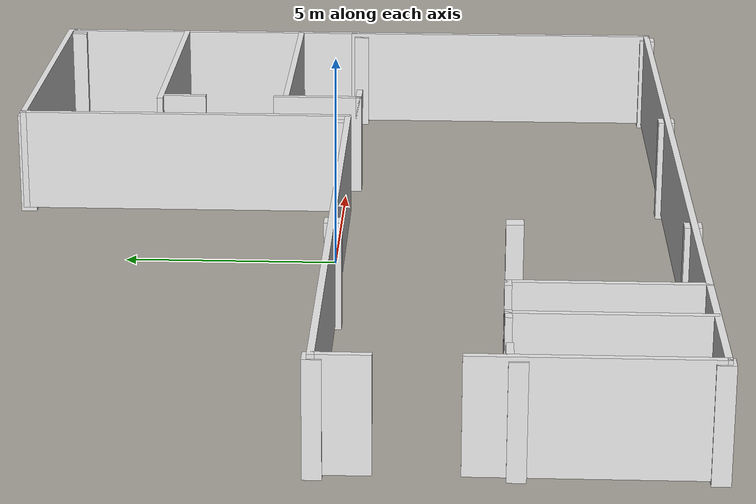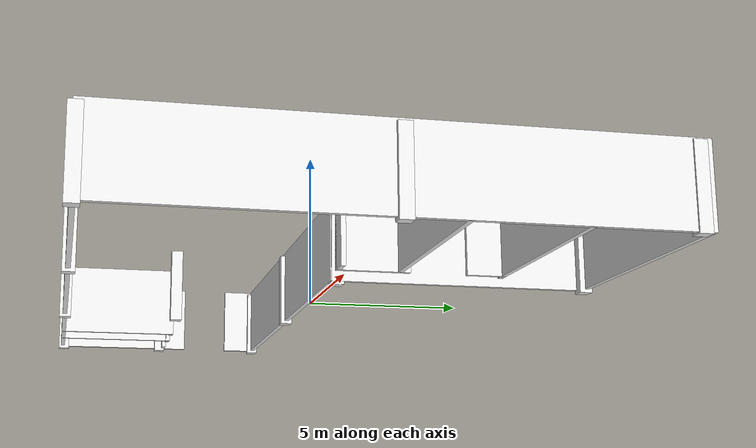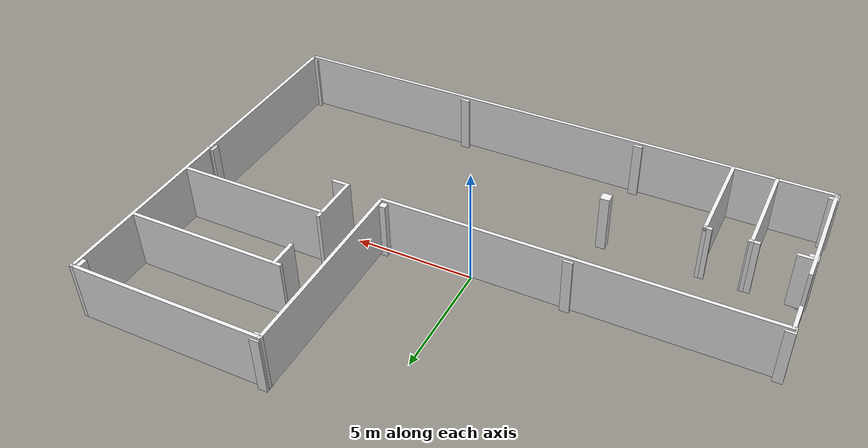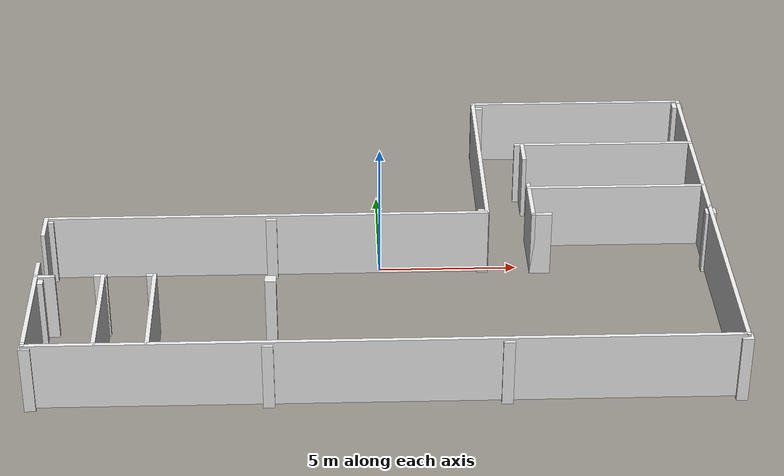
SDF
<?xml version='1.0'?>
<sdf version='1.6'>
  <model name='h_wall'>
    <link name='Wall_1'>
      <pose frame=''>-4.06743 -0.107748 0 0 -0 3.14159</pose>
      <self_collide>0</self_collide>
      <kinematic>0</kinematic>
      <visual name='Wall_1_Visual'>
        <pose frame=''>0 0 1.25 0 -0 0</pose>
        <geometry>
          <box>
            <size>16 0.15 2.5</size>
          </box>
        </geometry>
        <material>
          <script>
            <uri>file://media/materials/scripts/gazebo.material</uri>
            <name>Gazebo/White</name>
          </script>
          <ambient>1 1 1 1</ambient>
          <diffuse>0.7 0.7 0.7 1</diffuse>
          <specular>0.01 0.01 0.01 1</specular>
          <emissive>0 0 0 1</emissive>
        </material>
        <cast_shadows>1</cast_shadows>
        <transparency>0</transparency>
      </visual>
      <collision name='Wall_1_Collision'>
        <laser_retro>0</laser_retro>
        <max_contacts>10</max_contacts>
        <pose frame=''>0 0 1.25 0 -0 0</pose>
        <geometry>
          <box>
            <size>16 0.15 2.5</size>
          </box>
        </geometry>
        <surface>
          <friction>
            <ode>
              <mu>1</mu>
              <mu2>1</mu2>
              <fdir1>0 0 0</fdir1>
              <slip1>0</slip1>
              <slip2>0</slip2>
            </ode>
            <torsional>
              <coefficient>1</coefficient>
              <patch_radius>0</patch_radius>
              <surface_radius>0</surface_radius>
              <use_patch_radius>1</use_patch_radius>
              <ode>
                <slip>0</slip>
              </ode>
            </torsional>
          </friction>
          <bounce>
            <restitution_coefficient>0</restitution_coefficient>
            <threshold>1e+06</threshold>
          </bounce>
          <contact>
            <collide_without_contact>0</collide_without_contact>
            <collide_without_contact_bitmask>1</collide_without_contact_bitmask>
            <collide_bitmask>1</collide_bitmask>
            <ode>
              <soft_cfm>0</soft_cfm>
              <soft_erp>0.2</soft_erp>
              <kp>1e+13</kp>
              <kd>1</kd>
              <max_vel>0.01</max_vel>
              <min_depth>0</min_depth>
            </ode>
            <bullet>
              <split_impulse>1</split_impulse>
              <split_impulse_penetration_threshold>-0.01</split_impulse_penetration_threshold>
              <soft_cfm>0</soft_cfm>
              <soft_erp>0.2</soft_erp>
              <kp>1e+13</kp>
              <kd>1</kd>
            </bullet>
          </contact>
        </surface>
      </collision>
    </link>
    <link name='Wall_10'>
      <pose frame=''>-0.032574 -8.025 0 0 -0 0</pose>
      <self_collide>0</self_collide>
      <kinematic>0</kinematic>
      <visual name='Wall_10_Visual'>
        <pose frame=''>0 0 1.25 0 -0 0</pose>
        <geometry>
          <box>
            <size>24 0.15 2.5</size>
          </box>
        </geometry>
        <material>
          <script>
            <uri>file://media/materials/scripts/gazebo.material</uri>
            <name>Gazebo/White</name>
          </script>
          <ambient>1 1 1 1</ambient>
          <diffuse>0.7 0.7 0.7 1</diffuse>
          <specular>0.01 0.01 0.01 1</specular>
          <emissive>0 0 0 1</emissive>
        </material>
        <cast_shadows>1</cast_shadows>
        <transparency>0</transparency>
      </visual>
      <collision name='Wall_10_Collision'>
        <laser_retro>0</laser_retro>
        <max_contacts>10</max_contacts>
        <pose frame=''>0 0 1.25 0 -0 0</pose>
        <geometry>
          <box>
            <size>24 0.15 2.5</size>
          </box>
        </geometry>
        <surface>
          <friction>
            <ode>
              <mu>1</mu>
              <mu2>1</mu2>
              <fdir1>0 0 0</fdir1>
              <slip1>0</slip1>
              <slip2>0</slip2>
            </ode>
            <torsional>
              <coefficient>1</coefficient>
              <patch_radius>0</patch_radius>
              <surface_radius>0</surface_radius>
              <use_patch_radius>1</use_patch_radius>
              <ode>
                <slip>0</slip>
              </ode>
            </torsional>
          </friction>
          <bounce>
            <restitution_coefficient>0</restitution_coefficient>
            <threshold>1e+06</threshold>
          </bounce>
          <contact>
            <collide_without_contact>0</collide_without_contact>
            <collide_without_contact_bitmask>1</collide_without_contact_bitmask>
            <collide_bitmask>1</collide_bitmask>
            <ode>
              <soft_cfm>0</soft_cfm>
              <soft_erp>0.2</soft_erp>
              <kp>1e+13</kp>
              <kd>1</kd>
              <max_vel>0.01</max_vel>
              <min_depth>0</min_depth>
            </ode>
            <bullet>
              <split_impulse>1</split_impulse>
              <split_impulse_penetration_threshold>-0.01</split_impulse_penetration_threshold>
              <soft_cfm>0</soft_cfm>
              <soft_erp>0.2</soft_erp>
              <kp>1e+13</kp>
              <kd>1</kd>
            </bullet>
          </contact>
        </surface>
      </collision>
    </link>
    <link name='Wall_11'>
      <pose frame=''>11.9424 -8.025 0 0 -0 0</pose>
      <self_collide>0</self_collide>
      <kinematic>0</kinematic>
      <visual name='Wall_11_Visual'>
        <pose frame=''>0 0 1.25 0 -0 0</pose>
        <geometry>
          <box>
            <size>0.25 0.15 2.5</size>
          </box>
        </geometry>
        <material>
          <script>
            <uri>file://media/materials/scripts/gazebo.material</uri>
            <name>Gazebo/White</name>
          </script>
          <ambient>1 1 1 1</ambient>
          <diffuse>0.7 0.7 0.7 1</diffuse>
          <specular>0.01 0.01 0.01 1</specular>
          <emissive>0 0 0 1</emissive>
        </material>
        <cast_shadows>1</cast_shadows>
        <transparency>0</transparency>
      </visual>
      <collision name='Wall_11_Collision'>
        <laser_retro>0</laser_retro>
        <max_contacts>10</max_contacts>
        <pose frame=''>0 0 1.25 0 -0 0</pose>
        <geometry>
          <box>
            <size>0.25 0.15 2.5</size>
          </box>
        </geometry>
        <surface>
          <friction>
            <ode>
              <mu>1</mu>
              <mu2>1</mu2>
              <fdir1>0 0 0</fdir1>
              <slip1>0</slip1>
              <slip2>0</slip2>
            </ode>
            <torsional>
              <coefficient>1</coefficient>
              <patch_radius>0</patch_radius>
              <surface_radius>0</surface_radius>
              <use_patch_radius>1</use_patch_radius>
              <ode>
                <slip>0</slip>
              </ode>
            </torsional>
          </friction>
          <bounce>
            <restitution_coefficient>0</restitution_coefficient>
            <threshold>1e+06</threshold>
          </bounce>
          <contact>
            <collide_without_contact>0</collide_without_contact>
            <collide_without_contact_bitmask>1</collide_without_contact_bitmask>
            <collide_bitmask>1</collide_bitmask>
            <ode>
              <soft_cfm>0</soft_cfm>
              <soft_erp>0.2</soft_erp>
              <kp>1e+13</kp>
              <kd>1</kd>
              <max_vel>0.01</max_vel>
              <min_depth>0</min_depth>
            </ode>
            <bullet>
              <split_impulse>1</split_impulse>
              <split_impulse_penetration_threshold>-0.01</split_impulse_penetration_threshold>
              <soft_cfm>0</soft_cfm>
              <soft_erp>0.2</soft_erp>
              <kp>1e+13</kp>
              <kd>1</kd>
            </bullet>
          </contact>
        </surface>
      </collision>
    </link>
    <link name='Wall_12'>
      <pose frame=''>11.9924 -3.975 0 0 -0 1.5708</pose>
      <self_collide>0</self_collide>
      <kinematic>0</kinematic>
      <visual name='Wall_12_Visual'>
        <pose frame=''>0 0 1.25 0 -0 0</pose>
        <geometry>
          <box>
            <size>8.25 0.15 2.5</size>
          </box>
        </geometry>
        <material>
          <script>
            <uri>file://media/materials/scripts/gazebo.material</uri>
            <name>Gazebo/White</name>
          </script>
          <ambient>1 1 1 1</ambient>
          <diffuse>0.7 0.7 0.7 1</diffuse>
          <specular>0.01 0.01 0.01 1</specular>
          <emissive>0 0 0 1</emissive>
        </material>
        <cast_shadows>1</cast_shadows>
        <transparency>0</transparency>
      </visual>
      <collision name='Wall_12_Collision'>
        <laser_retro>0</laser_retro>
        <max_contacts>10</max_contacts>
        <pose frame=''>0 0 1.25 0 -0 0</pose>
        <geometry>
          <box>
            <size>8.25 0.15 2.5</size>
          </box>
        </geometry>
        <surface>
          <friction>
            <ode>
              <mu>1</mu>
              <mu2>1</mu2>
              <fdir1>0 0 0</fdir1>
              <slip1>0</slip1>
              <slip2>0</slip2>
            </ode>
            <torsional>
              <coefficient>1</coefficient>
              <patch_radius>0</patch_radius>
              <surface_radius>0</surface_radius>
              <use_patch_radius>1</use_patch_radius>
              <ode>
                <slip>0</slip>
              </ode>
            </torsional>
          </friction>
          <bounce>
            <restitution_coefficient>0</restitution_coefficient>
            <threshold>1e+06</threshold>
          </bounce>
          <contact>
            <collide_without_contact>0</collide_without_contact>
            <collide_without_contact_bitmask>1</collide_without_contact_bitmask>
            <collide_bitmask>1</collide_bitmask>
            <ode>
              <soft_cfm>0</soft_cfm>
              <soft_erp>0.2</soft_erp>
              <kp>1e+13</kp>
              <kd>1</kd>
              <max_vel>0.01</max_vel>
              <min_depth>0</min_depth>
            </ode>
            <bullet>
              <split_impulse>1</split_impulse>
              <split_impulse_penetration_threshold>-0.01</split_impulse_penetration_threshold>
              <soft_cfm>0</soft_cfm>
              <soft_erp>0.2</soft_erp>
              <kp>1e+13</kp>
              <kd>1</kd>
            </bullet>
          </contact>
        </surface>
      </collision>
    </link>
    <link name='Wall_13'>
      <pose frame=''>11.9924 4 0 0 -0 1.5708</pose>
      <inertial>
        <mass>1</mass>
        <pose frame=''>0 0 0 0 -0 0</pose>
        <inertia>
          <ixx>1</ixx>
          <ixy>0</ixy>
          <ixz>0</ixz>
          <iyy>1</iyy>
          <iyz>0</iyz>
          <izz>1</izz>
        </inertia>
      </inertial>
      <self_collide>0</self_collide>
      <kinematic>0</kinematic>
      <visual name='Wall_13_Visual'>
        <pose frame=''>0 0 1.25 0 -0 0</pose>
        <geometry>
          <box>
            <size>8 0.15 2.5</size>
          </box>
        </geometry>
        <material>
          <script>
            <uri>file://media/materials/scripts/gazebo.material</uri>
            <name>Gazebo/White</name>
          </script>
          <ambient>1 1 1 1</ambient>
          <diffuse>0.7 0.7 0.7 1</diffuse>
          <specular>0.01 0.01 0.01 1</specular>
          <emissive>0 0 0 1</emissive>
          <shader type='vertex'>
            <normal_map>__default__</normal_map>
          </shader>
        </material>
        <cast_shadows>1</cast_shadows>
        <transparency>0</transparency>
      </visual>
      <collision name='Wall_13_Collision'>
        <laser_retro>0</laser_retro>
        <max_contacts>10</max_contacts>
        <pose frame=''>0 0 1.25 0 -0 0</pose>
        <geometry>
          <box>
            <size>8 0.15 2.5</size>
          </box>
        </geometry>
        <surface>
          <friction>
            <ode>
              <mu>1</mu>
              <mu2>1</mu2>
              <fdir1>0 0 0</fdir1>
              <slip1>0</slip1>
              <slip2>0</slip2>
            </ode>
            <torsional>
              <coefficient>1</coefficient>
              <patch_radius>0</patch_radius>
              <surface_radius>0</surface_radius>
              <use_patch_radius>1</use_patch_radius>
              <ode>
                <slip>0</slip>
              </ode>
            </torsional>
          </friction>
          <bounce>
            <restitution_coefficient>0</restitution_coefficient>
            <threshold>1e+06</threshold>
          </bounce>
          <contact>
            <collide_without_contact>0</collide_without_contact>
            <collide_without_contact_bitmask>1</collide_without_contact_bitmask>
            <collide_bitmask>1</collide_bitmask>
            <ode>
              <soft_cfm>0</soft_cfm>
              <soft_erp>0.2</soft_erp>
              <kp>1e+13</kp>
              <kd>1</kd>
              <max_vel>0.01</max_vel>
              <min_depth>0</min_depth>
            </ode>
            <bullet>
              <split_impulse>1</split_impulse>
              <split_impulse_penetration_threshold>-0.01</split_impulse_penetration_threshold>
              <soft_cfm>0</soft_cfm>
              <soft_erp>0.2</soft_erp>
              <kp>1e+13</kp>
              <kd>1</kd>
            </bullet>
          </contact>
        </surface>
      </collision>
    </link>
    <link name='Wall_14'>
      <pose frame=''>11.9924 7.925 0 0 -0 0</pose>
      <self_collide>0</self_collide>
      <kinematic>0</kinematic>
      <visual name='Wall_14_Visual'>
        <pose frame=''>0 0 1.25 0 -0 0</pose>
        <geometry>
          <box>
            <size>0.15 0.15 2.5</size>
          </box>
        </geometry>
        <material>
          <script>
            <uri>file://media/materials/scripts/gazebo.material</uri>
            <name>Gazebo/White</name>
          </script>
          <ambient>1 1 1 1</ambient>
          <diffuse>0.7 0.7 0.7 1</diffuse>
          <specular>0.01 0.01 0.01 1</specular>
          <emissive>0 0 0 1</emissive>
        </material>
        <cast_shadows>1</cast_shadows>
        <transparency>0</transparency>
      </visual>
      <collision name='Wall_14_Collision'>
        <laser_retro>0</laser_retro>
        <max_contacts>10</max_contacts>
        <pose frame=''>0 0 1.25 0 -0 0</pose>
        <geometry>
          <box>
            <size>0.15 0.15 2.5</size>
          </box>
        </geometry>
        <surface>
          <friction>
            <ode>
              <mu>1</mu>
              <mu2>1</mu2>
              <fdir1>0 0 0</fdir1>
              <slip1>0</slip1>
              <slip2>0</slip2>
            </ode>
            <torsional>
              <coefficient>1</coefficient>
              <patch_radius>0</patch_radius>
              <surface_radius>0</surface_radius>
              <use_patch_radius>1</use_patch_radius>
              <ode>
                <slip>0</slip>
              </ode>
            </torsional>
          </friction>
          <bounce>
            <restitution_coefficient>0</restitution_coefficient>
            <threshold>1e+06</threshold>
          </bounce>
          <contact>
            <collide_without_contact>0</collide_without_contact>
            <collide_without_contact_bitmask>1</collide_without_contact_bitmask>
            <collide_bitmask>1</collide_bitmask>
            <ode>
              <soft_cfm>0</soft_cfm>
              <soft_erp>0.2</soft_erp>
              <kp>1e+13</kp>
              <kd>1</kd>
              <max_vel>0.01</max_vel>
              <min_depth>0</min_depth>
            </ode>
            <bullet>
              <split_impulse>1</split_impulse>
              <split_impulse_penetration_threshold>-0.01</split_impulse_penetration_threshold>
              <soft_cfm>0</soft_cfm>
              <soft_erp>0.2</soft_erp>
              <kp>1e+13</kp>
              <kd>1</kd>
            </bullet>
          </contact>
        </surface>
      </collision>
    </link>
    <link name='Wall_15'>
      <pose frame=''>11.9924 7.975 0 0 -0 1.5708</pose>
      <self_collide>0</self_collide>
      <kinematic>0</kinematic>
      <visual name='Wall_15_Visual'>
        <pose frame=''>0 0 1.25 0 -0 0</pose>
        <geometry>
          <box>
            <size>0.25 0.15 2.5</size>
          </box>
        </geometry>
        <material>
          <script>
            <uri>file://media/materials/scripts/gazebo.material</uri>
            <name>Gazebo/White</name>
          </script>
          <ambient>1 1 1 1</ambient>
          <diffuse>0.7 0.7 0.7 1</diffuse>
          <specular>0.01 0.01 0.01 1</specular>
          <emissive>0 0 0 1</emissive>
        </material>
        <cast_shadows>1</cast_shadows>
        <transparency>0</transparency>
      </visual>
      <collision name='Wall_15_Collision'>
        <laser_retro>0</laser_retro>
        <max_contacts>10</max_contacts>
        <pose frame=''>0 0 1.25 0 -0 0</pose>
        <geometry>
          <box>
            <size>0.25 0.15 2.5</size>
          </box>
        </geometry>
        <surface>
          <friction>
            <ode>
              <mu>1</mu>
              <mu2>1</mu2>
              <fdir1>0 0 0</fdir1>
              <slip1>0</slip1>
              <slip2>0</slip2>
            </ode>
            <torsional>
              <coefficient>1</coefficient>
              <patch_radius>0</patch_radius>
              <surface_radius>0</surface_radius>
              <use_patch_radius>1</use_patch_radius>
              <ode>
                <slip>0</slip>
              </ode>
            </torsional>
          </friction>
          <bounce>
            <restitution_coefficient>0</restitution_coefficient>
            <threshold>1e+06</threshold>
          </bounce>
          <contact>
            <collide_without_contact>0</collide_without_contact>
            <collide_without_contact_bitmask>1</collide_without_contact_bitmask>
            <collide_bitmask>1</collide_bitmask>
            <ode>
              <soft_cfm>0</soft_cfm>
              <soft_erp>0.2</soft_erp>
              <kp>1e+13</kp>
              <kd>1</kd>
              <max_vel>0.01</max_vel>
              <min_depth>0</min_depth>
            </ode>
            <bullet>
              <split_impulse>1</split_impulse>
              <split_impulse_penetration_threshold>-0.01</split_impulse_penetration_threshold>
              <soft_cfm>0</soft_cfm>
              <soft_erp>0.2</soft_erp>
              <kp>1e+13</kp>
              <kd>1</kd>
            </bullet>
          </contact>
        </surface>
      </collision>
    </link>
    <link name='Wall_16'>
      <pose frame=''>7.94243 8.025 0 0 -0 3.14159</pose>
      <self_collide>0</self_collide>
      <kinematic>0</kinematic>
      <visual name='Wall_16_Visual'>
        <pose frame=''>0 0 1.25 0 -0 0</pose>
        <geometry>
          <box>
            <size>8.25 0.15 2.5</size>
          </box>
        </geometry>
        <material>
          <script>
            <uri>file://media/materials/scripts/gazebo.material</uri>
            <name>Gazebo/White</name>
          </script>
          <ambient>1 1 1 1</ambient>
          <diffuse>0.7 0.7 0.7 1</diffuse>
          <specular>0.01 0.01 0.01 1</specular>
          <emissive>0 0 0 1</emissive>
        </material>
        <cast_shadows>1</cast_shadows>
        <transparency>0</transparency>
      </visual>
      <collision name='Wall_16_Collision'>
        <laser_retro>0</laser_retro>
        <max_contacts>10</max_contacts>
        <pose frame=''>0 0 1.25 0 -0 0</pose>
        <geometry>
          <box>
            <size>8.25 0.15 2.5</size>
          </box>
        </geometry>
        <surface>
          <friction>
            <ode>
              <mu>1</mu>
              <mu2>1</mu2>
              <fdir1>0 0 0</fdir1>
              <slip1>0</slip1>
              <slip2>0</slip2>
            </ode>
            <torsional>
              <coefficient>1</coefficient>
              <patch_radius>0</patch_radius>
              <surface_radius>0</surface_radius>
              <use_patch_radius>1</use_patch_radius>
              <ode>
                <slip>0</slip>
              </ode>
            </torsional>
          </friction>
          <bounce>
            <restitution_coefficient>0</restitution_coefficient>
            <threshold>1e+06</threshold>
          </bounce>
          <contact>
            <collide_without_contact>0</collide_without_contact>
            <collide_without_contact_bitmask>1</collide_without_contact_bitmask>
            <collide_bitmask>1</collide_bitmask>
            <ode>
              <soft_cfm>0</soft_cfm>
              <soft_erp>0.2</soft_erp>
              <kp>1e+13</kp>
              <kd>1</kd>
              <max_vel>0.01</max_vel>
              <min_depth>0</min_depth>
            </ode>
            <bullet>
              <split_impulse>1</split_impulse>
              <split_impulse_penetration_threshold>-0.01</split_impulse_penetration_threshold>
              <soft_cfm>0</soft_cfm>
              <soft_erp>0.2</soft_erp>
              <kp>1e+13</kp>
              <kd>1</kd>
            </bullet>
          </contact>
        </surface>
      </collision>
    </link>
    <link name='Wall_17'>
      <pose frame=''>3.89243 3.975 0 0 0 -1.5708</pose>
      <self_collide>0</self_collide>
      <kinematic>0</kinematic>
      <visual name='Wall_17_Visual'>
        <pose frame=''>0 0 1.25 0 -0 0</pose>
        <geometry>
          <box>
            <size>8.25 0.15 2.5</size>
          </box>
        </geometry>
        <material>
          <script>
            <uri>file://media/materials/scripts/gazebo.material</uri>
            <name>Gazebo/White</name>
          </script>
          <ambient>1 1 1 1</ambient>
          <diffuse>0.7 0.7 0.7 1</diffuse>
          <specular>0.01 0.01 0.01 1</specular>
          <emissive>0 0 0 1</emissive>
        </material>
        <cast_shadows>1</cast_shadows>
        <transparency>0</transparency>
      </visual>
      <collision name='Wall_17_Collision'>
        <laser_retro>0</laser_retro>
        <max_contacts>10</max_contacts>
        <pose frame=''>0 0 1.25 0 -0 0</pose>
        <geometry>
          <box>
            <size>8.25 0.15 2.5</size>
          </box>
        </geometry>
        <surface>
          <friction>
            <ode>
              <mu>1</mu>
              <mu2>1</mu2>
              <fdir1>0 0 0</fdir1>
              <slip1>0</slip1>
              <slip2>0</slip2>
            </ode>
            <torsional>
              <coefficient>1</coefficient>
              <patch_radius>0</patch_radius>
              <surface_radius>0</surface_radius>
              <use_patch_radius>1</use_patch_radius>
              <ode>
                <slip>0</slip>
              </ode>
            </torsional>
          </friction>
          <bounce>
            <restitution_coefficient>0</restitution_coefficient>
            <threshold>1e+06</threshold>
          </bounce>
          <contact>
            <collide_without_contact>0</collide_without_contact>
            <collide_without_contact_bitmask>1</collide_without_contact_bitmask>
            <collide_bitmask>1</collide_bitmask>
            <ode>
              <soft_cfm>0</soft_cfm>
              <soft_erp>0.2</soft_erp>
              <kp>1e+13</kp>
              <kd>1</kd>
              <max_vel>0.01</max_vel>
              <min_depth>0</min_depth>
            </ode>
            <bullet>
              <split_impulse>1</split_impulse>
              <split_impulse_penetration_threshold>-0.01</split_impulse_penetration_threshold>
              <soft_cfm>0</soft_cfm>
              <soft_erp>0.2</soft_erp>
              <kp>1e+13</kp>
              <kd>1</kd>
            </bullet>
          </contact>
        </surface>
      </collision>
    </link>
    <link name='Wall_19'>
      <pose frame=''>-11.6601 -3.90046 0 0 -0 0</pose>
      <self_collide>0</self_collide>
      <kinematic>0</kinematic>
      <inertial>
        <inertia>
          <ixx>nan</ixx>
          <ixy>0</ixy>
          <ixz>0</ixz>
          <iyy>nan</iyy>
          <iyz>0</iyz>
          <izz>nan</izz>
        </inertia>
        <mass>0</mass>
        <pose frame=''>0 0 0 0 -0 0</pose>
      </inertial>
      <visual name='Wall_19_Visual'>
        <pose frame=''>0 0 1.25 0 -0 0</pose>
        <geometry>
          <box>
            <size>0.736562 0.15 2.5</size>
          </box>
        </geometry>
        <material>
          <script>
            <uri>file://media/materials/scripts/gazebo.material</uri>
            <name>Gazebo/White</name>
          </script>
          <ambient>1 1 1 1</ambient>
          <diffuse>0.7 0.7 0.7 1</diffuse>
          <specular>0.01 0.01 0.01 1</specular>
          <emissive>0 0 0 1</emissive>
        </material>
        <cast_shadows>1</cast_shadows>
        <transparency>0</transparency>
      </visual>
      <collision name='Wall_19_Collision'>
        <laser_retro>0</laser_retro>
        <max_contacts>10</max_contacts>
        <pose frame=''>0 0 1.25 0 -0 0</pose>
        <geometry>
          <box>
            <size>0.736562 0.15 2.5</size>
          </box>
        </geometry>
        <surface>
          <friction>
            <ode>
              <mu>1</mu>
              <mu2>1</mu2>
              <fdir1>0 0 0</fdir1>
              <slip1>0</slip1>
              <slip2>0</slip2>
            </ode>
            <torsional>
              <coefficient>1</coefficient>
              <patch_radius>0</patch_radius>
              <surface_radius>0</surface_radius>
              <use_patch_radius>1</use_patch_radius>
              <ode>
                <slip>0</slip>
              </ode>
            </torsional>
          </friction>
          <bounce>
            <restitution_coefficient>0</restitution_coefficient>
            <threshold>1e+06</threshold>
          </bounce>
          <contact>
            <collide_without_contact>0</collide_without_contact>
            <collide_without_contact_bitmask>1</collide_without_contact_bitmask>
            <collide_bitmask>1</collide_bitmask>
            <ode>
              <soft_cfm>0</soft_cfm>
              <soft_erp>0.2</soft_erp>
              <kp>1e+13</kp>
              <kd>1</kd>
              <max_vel>0.01</max_vel>
              <min_depth>0</min_depth>
            </ode>
            <bullet>
              <split_impulse>1</split_impulse>
              <split_impulse_penetration_threshold>-0.01</split_impulse_penetration_threshold>
              <soft_cfm>0</soft_cfm>
              <soft_erp>0.2</soft_erp>
              <kp>1e+13</kp>
              <kd>1</kd>
            </bullet>
          </contact>
        </surface>
      </collision>
    </link>
    <link name='Wall_2'>
      <pose frame=''>-11.9924 -0.657748 0 0 0 -1.5708</pose>
      <self_collide>0</self_collide>
      <kinematic>0</kinematic>
      <visual name='Wall_2_Visual'>
        <pose frame=''>0 0 1.25 0 -0 0</pose>
        <geometry>
          <box>
            <size>1.25 0.15 2.5</size>
          </box>
        </geometry>
        <material>
          <script>
            <uri>file://media/materials/scripts/gazebo.material</uri>
            <name>Gazebo/White</name>
          </script>
          <ambient>1 1 1 1</ambient>
          <diffuse>0.7 0.7 0.7 1</diffuse>
          <specular>0.01 0.01 0.01 1</specular>
          <emissive>0 0 0 1</emissive>
        </material>
        <cast_shadows>1</cast_shadows>
        <transparency>0</transparency>
      </visual>
      <collision name='Wall_2_Collision'>
        <laser_retro>0</laser_retro>
        <max_contacts>10</max_contacts>
        <pose frame=''>0 0 1.25 0 -0 0</pose>
        <geometry>
          <box>
            <size>1.25 0.15 2.5</size>
          </box>
        </geometry>
        <surface>
          <friction>
            <ode>
              <mu>1</mu>
              <mu2>1</mu2>
              <fdir1>0 0 0</fdir1>
              <slip1>0</slip1>
              <slip2>0</slip2>
            </ode>
            <torsional>
              <coefficient>1</coefficient>
              <patch_radius>0</patch_radius>
              <surface_radius>0</surface_radius>
              <use_patch_radius>1</use_patch_radius>
              <ode>
                <slip>0</slip>
              </ode>
            </torsional>
          </friction>
          <bounce>
            <restitution_coefficient>0</restitution_coefficient>
            <threshold>1e+06</threshold>
          </bounce>
          <contact>
            <collide_without_contact>0</collide_without_contact>
            <collide_without_contact_bitmask>1</collide_without_contact_bitmask>
            <collide_bitmask>1</collide_bitmask>
            <ode>
              <soft_cfm>0</soft_cfm>
              <soft_erp>0.2</soft_erp>
              <kp>1e+13</kp>
              <kd>1</kd>
              <max_vel>0.01</max_vel>
              <min_depth>0</min_depth>
            </ode>
            <bullet>
              <split_impulse>1</split_impulse>
              <split_impulse_penetration_threshold>-0.01</split_impulse_penetration_threshold>
              <soft_cfm>0</soft_cfm>
              <soft_erp>0.2</soft_erp>
              <kp>1e+13</kp>
              <kd>1</kd>
            </bullet>
          </contact>
        </surface>
      </collision>
    </link>
    <link name='Wall_21'>
      <pose frame=''>-9.73392 -3.90046 0 0 -0 0</pose>
      <self_collide>0</self_collide>
      <kinematic>0</kinematic>
      <inertial>
        <inertia>
          <ixx>nan</ixx>
          <ixy>0</ixy>
          <ixz>0</ixz>
          <iyy>nan</iyy>
          <iyz>0</iyz>
          <izz>nan</izz>
        </inertia>
        <mass>0</mass>
        <pose frame=''>0 0 0 0 -0 0</pose>
      </inertial>
      <visual name='Wall_21_Visual'>
        <pose frame=''>0 0 1.25 0 -0 0</pose>
        <geometry>
          <box>
            <size>0.453657 0.15 2.5</size>
          </box>
        </geometry>
        <material>
          <script>
            <uri>file://media/materials/scripts/gazebo.material</uri>
            <name>Gazebo/White</name>
          </script>
          <ambient>1 1 1 1</ambient>
          <diffuse>0.7 0.7 0.7 1</diffuse>
          <specular>0.01 0.01 0.01 1</specular>
          <emissive>0 0 0 1</emissive>
        </material>
        <cast_shadows>1</cast_shadows>
        <transparency>0</transparency>
      </visual>
      <collision name='Wall_21_Collision'>
        <laser_retro>0</laser_retro>
        <max_contacts>10</max_contacts>
        <pose frame=''>0 0 1.25 0 -0 0</pose>
        <geometry>
          <box>
            <size>0.453657 0.15 2.5</size>
          </box>
        </geometry>
        <surface>
          <friction>
            <ode>
              <mu>1</mu>
              <mu2>1</mu2>
              <fdir1>0 0 0</fdir1>
              <slip1>0</slip1>
              <slip2>0</slip2>
            </ode>
            <torsional>
              <coefficient>1</coefficient>
              <patch_radius>0</patch_radius>
              <surface_radius>0</surface_radius>
              <use_patch_radius>1</use_patch_radius>
              <ode>
                <slip>0</slip>
              </ode>
            </torsional>
          </friction>
          <bounce>
            <restitution_coefficient>0</restitution_coefficient>
            <threshold>1e+06</threshold>
          </bounce>
          <contact>
            <collide_without_contact>0</collide_without_contact>
            <collide_without_contact_bitmask>1</collide_without_contact_bitmask>
            <collide_bitmask>1</collide_bitmask>
            <ode>
              <soft_cfm>0</soft_cfm>
              <soft_erp>0.2</soft_erp>
              <kp>1e+13</kp>
              <kd>1</kd>
              <max_vel>0.01</max_vel>
              <min_depth>0</min_depth>
            </ode>
            <bullet>
              <split_impulse>1</split_impulse>
              <split_impulse_penetration_threshold>-0.01</split_impulse_penetration_threshold>
              <soft_cfm>0</soft_cfm>
              <soft_erp>0.2</soft_erp>
              <kp>1e+13</kp>
              <kd>1</kd>
            </bullet>
          </contact>
        </surface>
      </collision>
    </link>
    <link name='Wall_24'>
      <pose frame=''>-9.64084 -5.94162 0 0 -0 1.5708</pose>
      <self_collide>0</self_collide>
      <kinematic>0</kinematic>
      <visual name='Wall_24_Visual'>
        <pose frame=''>0 0 1.25 0 -0 0</pose>
        <geometry>
          <box>
            <size>4.25 0.15 2.5</size>
          </box>
        </geometry>
        <material>
          <script>
            <uri>file://media/materials/scripts/gazebo.material</uri>
            <name>Gazebo/White</name>
          </script>
          <ambient>1 1 1 1</ambient>
          <diffuse>0.7 0.7 0.7 1</diffuse>
          <specular>0.01 0.01 0.01 1</specular>
          <emissive>0 0 0 1</emissive>
        </material>
        <cast_shadows>1</cast_shadows>
        <transparency>0</transparency>
      </visual>
      <collision name='Wall_24_Collision'>
        <laser_retro>0</laser_retro>
        <max_contacts>10</max_contacts>
        <pose frame=''>0 0 1.25 0 -0 0</pose>
        <geometry>
          <box>
            <size>4.25 0.15 2.5</size>
          </box>
        </geometry>
        <surface>
          <friction>
            <ode>
              <mu>1</mu>
              <mu2>1</mu2>
              <fdir1>0 0 0</fdir1>
              <slip1>0</slip1>
              <slip2>0</slip2>
            </ode>
            <torsional>
              <coefficient>1</coefficient>
              <patch_radius>0</patch_radius>
              <surface_radius>0</surface_radius>
              <use_patch_radius>1</use_patch_radius>
              <ode>
                <slip>0</slip>
              </ode>
            </torsional>
          </friction>
          <bounce>
            <restitution_coefficient>0</restitution_coefficient>
            <threshold>1e+06</threshold>
          </bounce>
          <contact>
            <collide_without_contact>0</collide_without_contact>
            <collide_without_contact_bitmask>1</collide_without_contact_bitmask>
            <collide_bitmask>1</collide_bitmask>
            <ode>
              <soft_cfm>0</soft_cfm>
              <soft_erp>0.2</soft_erp>
              <kp>1e+13</kp>
              <kd>1</kd>
              <max_vel>0.01</max_vel>
              <min_depth>0</min_depth>
            </ode>
            <bullet>
              <split_impulse>1</split_impulse>
              <split_impulse_penetration_threshold>-0.01</split_impulse_penetration_threshold>
              <soft_cfm>0</soft_cfm>
              <soft_erp>0.2</soft_erp>
              <kp>1e+13</kp>
              <kd>1</kd>
            </bullet>
          </contact>
        </surface>
      </collision>
    </link>
    <link name='Wall_30'>
      <pose frame=''>-7.97483 -3.91861 0 0 -0 0</pose>
      <self_collide>0</self_collide>
      <kinematic>0</kinematic>
      <inertial>
        <inertia>
          <ixx>nan</ixx>
          <ixy>0</ixy>
          <ixz>0</ixz>
          <iyy>nan</iyy>
          <iyz>0</iyz>
          <izz>nan</izz>
        </inertia>
        <mass>0</mass>
        <pose frame=''>0 0 0 0 -0 0</pose>
      </inertial>
      <visual name='Wall_30_Visual'>
        <pose frame=''>0 0 1.25 0 -0 0</pose>
        <geometry>
          <box>
            <size>0.337076 0.15 2.5</size>
          </box>
        </geometry>
        <material>
          <script>
            <uri>file://media/materials/scripts/gazebo.material</uri>
            <name>Gazebo/White</name>
          </script>
          <ambient>1 1 1 1</ambient>
          <diffuse>0.7 0.7 0.7 1</diffuse>
          <specular>0.01 0.01 0.01 1</specular>
          <emissive>0 0 0 1</emissive>
        </material>
        <cast_shadows>1</cast_shadows>
        <transparency>0</transparency>
      </visual>
      <collision name='Wall_30_Collision'>
        <laser_retro>0</laser_retro>
        <max_contacts>10</max_contacts>
        <pose frame=''>0 0 1.25 0 -0 0</pose>
        <geometry>
          <box>
            <size>0.337076 0.15 2.5</size>
          </box>
        </geometry>
        <surface>
          <friction>
            <ode>
              <mu>1</mu>
              <mu2>1</mu2>
              <fdir1>0 0 0</fdir1>
              <slip1>0</slip1>
              <slip2>0</slip2>
            </ode>
            <torsional>
              <coefficient>1</coefficient>
              <patch_radius>0</patch_radius>
              <surface_radius>0</surface_radius>
              <use_patch_radius>1</use_patch_radius>
              <ode>
                <slip>0</slip>
              </ode>
            </torsional>
          </friction>
          <bounce>
            <restitution_coefficient>0</restitution_coefficient>
            <threshold>1e+06</threshold>
          </bounce>
          <contact>
            <collide_without_contact>0</collide_without_contact>
            <collide_without_contact_bitmask>1</collide_without_contact_bitmask>
            <collide_bitmask>1</collide_bitmask>
            <ode>
              <soft_cfm>0</soft_cfm>
              <soft_erp>0.2</soft_erp>
              <kp>1e+13</kp>
              <kd>1</kd>
              <max_vel>0.01</max_vel>
              <min_depth>0</min_depth>
            </ode>
            <bullet>
              <split_impulse>1</split_impulse>
              <split_impulse_penetration_threshold>-0.01</split_impulse_penetration_threshold>
              <soft_cfm>0</soft_cfm>
              <soft_erp>0.2</soft_erp>
              <kp>1e+13</kp>
              <kd>1</kd>
            </bullet>
          </contact>
        </surface>
      </collision>
    </link>
    <link name='Wall_31'>
      <pose frame=''>-7.86723 -5.96861 0 0 0 -1.5708</pose>
      <self_collide>0</self_collide>
      <kinematic>0</kinematic>
      <visual name='Wall_31_Visual'>
        <pose frame=''>0 0 1.25 0 -0 0</pose>
        <geometry>
          <box>
            <size>4.25 0.15 2.5</size>
          </box>
        </geometry>
        <material>
          <script>
            <uri>file://media/materials/scripts/gazebo.material</uri>
            <name>Gazebo/White</name>
          </script>
          <ambient>1 1 1 1</ambient>
          <diffuse>0.7 0.7 0.7 1</diffuse>
          <specular>0.01 0.01 0.01 1</specular>
          <emissive>0 0 0 1</emissive>
        </material>
        <cast_shadows>1</cast_shadows>
        <transparency>0</transparency>
      </visual>
      <collision name='Wall_31_Collision'>
        <laser_retro>0</laser_retro>
        <max_contacts>10</max_contacts>
        <pose frame=''>0 0 1.25 0 -0 0</pose>
        <geometry>
          <box>
            <size>4.25 0.15 2.5</size>
          </box>
        </geometry>
        <surface>
          <friction>
            <ode>
              <mu>1</mu>
              <mu2>1</mu2>
              <fdir1>0 0 0</fdir1>
              <slip1>0</slip1>
              <slip2>0</slip2>
            </ode>
            <torsional>
              <coefficient>1</coefficient>
              <patch_radius>0</patch_radius>
              <surface_radius>0</surface_radius>
              <use_patch_radius>1</use_patch_radius>
              <ode>
                <slip>0</slip>
              </ode>
            </torsional>
          </friction>
          <bounce>
            <restitution_coefficient>0</restitution_coefficient>
            <threshold>1e+06</threshold>
          </bounce>
          <contact>
            <collide_without_contact>0</collide_without_contact>
            <collide_without_contact_bitmask>1</collide_without_contact_bitmask>
            <collide_bitmask>1</collide_bitmask>
            <ode>
              <soft_cfm>0</soft_cfm>
              <soft_erp>0.2</soft_erp>
              <kp>1e+13</kp>
              <kd>1</kd>
              <max_vel>0.01</max_vel>
              <min_depth>0</min_depth>
            </ode>
            <bullet>
              <split_impulse>1</split_impulse>
              <split_impulse_penetration_threshold>-0.01</split_impulse_penetration_threshold>
              <soft_cfm>0</soft_cfm>
              <soft_erp>0.2</soft_erp>
              <kp>1e+13</kp>
              <kd>1</kd>
            </bullet>
          </contact>
        </surface>
      </collision>
    </link>
    <link name='Wall_33'>
      <pose frame=''>8.6623 4.75744 0 0 -0 0</pose>
      <self_collide>0</self_collide>
      <kinematic>0</kinematic>
      <inertial>
        <inertia>
          <ixx>nan</ixx>
          <ixy>0</ixy>
          <ixz>0</ixz>
          <iyy>nan</iyy>
          <iyz>0</iyz>
          <izz>nan</izz>
        </inertia>
        <mass>0</mass>
        <pose frame=''>0 0 0 0 -0 0</pose>
      </inertial>
      <visual name='Wall_33_Visual'>
        <pose frame=''>0 0 1.25 0 -0 0</pose>
        <geometry>
          <box>
            <size>6.80324 0.15 2.5</size>
          </box>
        </geometry>
        <material>
          <script>
            <uri>file://media/materials/scripts/gazebo.material</uri>
            <name>Gazebo/White</name>
          </script>
          <ambient>1 1 1 1</ambient>
          <diffuse>0.7 0.7 0.7 1</diffuse>
          <specular>0.01 0.01 0.01 1</specular>
          <emissive>0 0 0 1</emissive>
        </material>
        <cast_shadows>1</cast_shadows>
        <transparency>0</transparency>
      </visual>
      <collision name='Wall_33_Collision'>
        <laser_retro>0</laser_retro>
        <max_contacts>10</max_contacts>
        <pose frame=''>0 0 1.25 0 -0 0</pose>
        <geometry>
          <box>
            <size>6.80324 0.15 2.5</size>
          </box>
        </geometry>
        <surface>
          <friction>
            <ode>
              <mu>1</mu>
              <mu2>1</mu2>
              <fdir1>0 0 0</fdir1>
              <slip1>0</slip1>
              <slip2>0</slip2>
            </ode>
            <torsional>
              <coefficient>1</coefficient>
              <patch_radius>0</patch_radius>
              <surface_radius>0</surface_radius>
              <use_patch_radius>1</use_patch_radius>
              <ode>
                <slip>0</slip>
              </ode>
            </torsional>
          </friction>
          <bounce>
            <restitution_coefficient>0</restitution_coefficient>
            <threshold>1e+06</threshold>
          </bounce>
          <contact>
            <collide_without_contact>0</collide_without_contact>
            <collide_without_contact_bitmask>1</collide_without_contact_bitmask>
            <collide_bitmask>1</collide_bitmask>
            <ode>
              <soft_cfm>0</soft_cfm>
              <soft_erp>0.2</soft_erp>
              <kp>1e+13</kp>
              <kd>1</kd>
              <max_vel>0.01</max_vel>
              <min_depth>0</min_depth>
            </ode>
            <bullet>
              <split_impulse>1</split_impulse>
              <split_impulse_penetration_threshold>-0.01</split_impulse_penetration_threshold>
              <soft_cfm>0</soft_cfm>
              <soft_erp>0.2</soft_erp>
              <kp>1e+13</kp>
              <kd>1</kd>
            </bullet>
          </contact>
        </surface>
      </collision>
    </link>
    <link name='Wall_35'>
      <pose frame=''>5.55705 4.2159 0 0 0 -1.5708</pose>
      <self_collide>0</self_collide>
      <kinematic>0</kinematic>
      <inertial>
        <inertia>
          <ixx>nan</ixx>
          <ixy>0</ixy>
          <ixz>0</ixz>
          <iyy>nan</iyy>
          <iyz>0</iyz>
          <izz>nan</izz>
        </inertia>
        <mass>0</mass>
        <pose frame=''>0 0 0 0 -0 0</pose>
      </inertial>
      <visual name='Wall_35_Visual'>
        <pose frame=''>0 0 1.25 0 -0 0</pose>
        <geometry>
          <box>
            <size>1.22204 0.15 2.5</size>
          </box>
        </geometry>
        <material>
          <script>
            <uri>file://media/materials/scripts/gazebo.material</uri>
            <name>Gazebo/White</name>
          </script>
          <ambient>1 1 1 1</ambient>
          <diffuse>0.7 0.7 0.7 1</diffuse>
          <specular>0.01 0.01 0.01 1</specular>
          <emissive>0 0 0 1</emissive>
        </material>
        <cast_shadows>1</cast_shadows>
        <transparency>0</transparency>
      </visual>
      <collision name='Wall_35_Collision'>
        <laser_retro>0</laser_retro>
        <max_contacts>10</max_contacts>
        <pose frame=''>0 0 1.25 0 -0 0</pose>
        <geometry>
          <box>
            <size>1.22204 0.15 2.5</size>
          </box>
        </geometry>
        <surface>
          <friction>
            <ode>
              <mu>1</mu>
              <mu2>1</mu2>
              <fdir1>0 0 0</fdir1>
              <slip1>0</slip1>
              <slip2>0</slip2>
            </ode>
            <torsional>
              <coefficient>1</coefficient>
              <patch_radius>0</patch_radius>
              <surface_radius>0</surface_radius>
              <use_patch_radius>1</use_patch_radius>
              <ode>
                <slip>0</slip>
              </ode>
            </torsional>
          </friction>
          <bounce>
            <restitution_coefficient>0</restitution_coefficient>
            <threshold>1e+06</threshold>
          </bounce>
          <contact>
            <collide_without_contact>0</collide_without_contact>
            <collide_without_contact_bitmask>1</collide_without_contact_bitmask>
            <collide_bitmask>1</collide_bitmask>
            <ode>
              <soft_cfm>0</soft_cfm>
              <soft_erp>0.2</soft_erp>
              <kp>1e+13</kp>
              <kd>1</kd>
              <max_vel>0.01</max_vel>
              <min_depth>0</min_depth>
            </ode>
            <bullet>
              <split_impulse>1</split_impulse>
              <split_impulse_penetration_threshold>-0.01</split_impulse_penetration_threshold>
              <soft_cfm>0</soft_cfm>
              <soft_erp>0.2</soft_erp>
              <kp>1e+13</kp>
              <kd>1</kd>
            </bullet>
          </contact>
        </surface>
      </collision>
    </link>
    <link name='Wall_37'>
      <pose frame=''>8.74527 1.55699 0 0 -0 0</pose>
      <self_collide>0</self_collide>
      <kinematic>0</kinematic>
      <visual name='Wall_37_Visual'>
        <pose frame=''>0 0 1.25 0 -0 0</pose>
        <geometry>
          <box>
            <size>6.5 0.15 2.5</size>
          </box>
        </geometry>
        <material>
          <script>
            <uri>file://media/materials/scripts/gazebo.material</uri>
            <name>Gazebo/White</name>
          </script>
          <ambient>1 1 1 1</ambient>
          <diffuse>0.7 0.7 0.7 1</diffuse>
          <specular>0.01 0.01 0.01 1</specular>
          <emissive>0 0 0 1</emissive>
        </material>
        <cast_shadows>1</cast_shadows>
        <transparency>0</transparency>
      </visual>
      <collision name='Wall_37_Collision'>
        <laser_retro>0</laser_retro>
        <max_contacts>10</max_contacts>
        <pose frame=''>0 0 1.25 0 -0 0</pose>
        <geometry>
          <box>
            <size>6.5 0.15 2.5</size>
          </box>
        </geometry>
        <surface>
          <friction>
            <ode>
              <mu>1</mu>
              <mu2>1</mu2>
              <fdir1>0 0 0</fdir1>
              <slip1>0</slip1>
              <slip2>0</slip2>
            </ode>
            <torsional>
              <coefficient>1</coefficient>
              <patch_radius>0</patch_radius>
              <surface_radius>0</surface_radius>
              <use_patch_radius>1</use_patch_radius>
              <ode>
                <slip>0</slip>
              </ode>
            </torsional>
          </friction>
          <bounce>
            <restitution_coefficient>0</restitution_coefficient>
            <threshold>1e+06</threshold>
          </bounce>
          <contact>
            <collide_without_contact>0</collide_without_contact>
            <collide_without_contact_bitmask>1</collide_without_contact_bitmask>
            <collide_bitmask>1</collide_bitmask>
            <ode>
              <soft_cfm>0</soft_cfm>
              <soft_erp>0.2</soft_erp>
              <kp>1e+13</kp>
              <kd>1</kd>
              <max_vel>0.01</max_vel>
              <min_depth>0</min_depth>
            </ode>
            <bullet>
              <split_impulse>1</split_impulse>
              <split_impulse_penetration_threshold>-0.01</split_impulse_penetration_threshold>
              <soft_cfm>0</soft_cfm>
              <soft_erp>0.2</soft_erp>
              <kp>1e+13</kp>
              <kd>1</kd>
            </bullet>
          </contact>
        </surface>
      </collision>
    </link>
    <link name='Wall_39'>
      <pose frame=''>5.54382 0.745041 0 0 0 -1.5708</pose>
      <self_collide>0</self_collide>
      <kinematic>0</kinematic>
      <visual name='Wall_39_Visual'>
        <pose frame=''>0 0 1.25 0 -0 0</pose>
        <geometry>
          <box>
            <size>2.25 0.15 2.5</size>
          </box>
        </geometry>
        <material>
          <script>
            <uri>file://media/materials/scripts/gazebo.material</uri>
            <name>Gazebo/White</name>
          </script>
          <ambient>1 1 1 1</ambient>
          <diffuse>0.7 0.7 0.7 1</diffuse>
          <specular>0.01 0.01 0.01 1</specular>
          <emissive>0 0 0 1</emissive>
        </material>
        <cast_shadows>1</cast_shadows>
        <transparency>0</transparency>
      </visual>
      <collision name='Wall_39_Collision'>
        <laser_retro>0</laser_retro>
        <max_contacts>10</max_contacts>
        <pose frame=''>0 0 1.25 0 -0 0</pose>
        <geometry>
          <box>
            <size>2.25 0.15 2.5</size>
          </box>
        </geometry>
        <surface>
          <friction>
            <ode>
              <mu>1</mu>
              <mu2>1</mu2>
              <fdir1>0 0 0</fdir1>
              <slip1>0</slip1>
              <slip2>0</slip2>
            </ode>
            <torsional>
              <coefficient>1</coefficient>
              <patch_radius>0</patch_radius>
              <surface_radius>0</surface_radius>
              <use_patch_radius>1</use_patch_radius>
              <ode>
                <slip>0</slip>
              </ode>
            </torsional>
          </friction>
          <bounce>
            <restitution_coefficient>0</restitution_coefficient>
            <threshold>1e+06</threshold>
          </bounce>
          <contact>
            <collide_without_contact>0</collide_without_contact>
            <collide_without_contact_bitmask>1</collide_without_contact_bitmask>
            <collide_bitmask>1</collide_bitmask>
            <ode>
              <soft_cfm>0</soft_cfm>
              <soft_erp>0.2</soft_erp>
              <kp>1e+13</kp>
              <kd>1</kd>
              <max_vel>0.01</max_vel>
              <min_depth>0</min_depth>
            </ode>
            <bullet>
              <split_impulse>1</split_impulse>
              <split_impulse_penetration_threshold>-0.01</split_impulse_penetration_threshold>
              <soft_cfm>0</soft_cfm>
              <soft_erp>0.2</soft_erp>
              <kp>1e+13</kp>
              <kd>1</kd>
            </bullet>
          </contact>
        </surface>
      </collision>
    </link>
    <link name='Wall_40'>
      <pose frame=''>5.84382 -0.304959 0 0 -0 0</pose>
      <self_collide>0</self_collide>
      <kinematic>0</kinematic>
      <visual name='Wall_40_Visual'>
        <pose frame=''>0 0 1.25 0 -0 0</pose>
        <geometry>
          <box>
            <size>0.75 0.15 2.5</size>
          </box>
        </geometry>
        <material>
          <script>
            <uri>file://media/materials/scripts/gazebo.material</uri>
            <name>Gazebo/White</name>
          </script>
          <ambient>1 1 1 1</ambient>
          <diffuse>0.7 0.7 0.7 1</diffuse>
          <specular>0.01 0.01 0.01 1</specular>
          <emissive>0 0 0 1</emissive>
        </material>
        <cast_shadows>1</cast_shadows>
        <transparency>0</transparency>
      </visual>
      <collision name='Wall_40_Collision'>
        <laser_retro>0</laser_retro>
        <max_contacts>10</max_contacts>
        <pose frame=''>0 0 1.25 0 -0 0</pose>
        <geometry>
          <box>
            <size>0.75 0.15 2.5</size>
          </box>
        </geometry>
        <surface>
          <friction>
            <ode>
              <mu>1</mu>
              <mu2>1</mu2>
              <fdir1>0 0 0</fdir1>
              <slip1>0</slip1>
              <slip2>0</slip2>
            </ode>
            <torsional>
              <coefficient>1</coefficient>
              <patch_radius>0</patch_radius>
              <surface_radius>0</surface_radius>
              <use_patch_radius>1</use_patch_radius>
              <ode>
                <slip>0</slip>
              </ode>
            </torsional>
          </friction>
          <bounce>
            <restitution_coefficient>0</restitution_coefficient>
            <threshold>1e+06</threshold>
          </bounce>
          <contact>
            <collide_without_contact>0</collide_without_contact>
            <collide_without_contact_bitmask>1</collide_without_contact_bitmask>
            <collide_bitmask>1</collide_bitmask>
            <ode>
              <soft_cfm>0</soft_cfm>
              <soft_erp>0.2</soft_erp>
              <kp>1e+13</kp>
              <kd>1</kd>
              <max_vel>0.01</max_vel>
              <min_depth>0</min_depth>
            </ode>
            <bullet>
              <split_impulse>1</split_impulse>
              <split_impulse_penetration_threshold>-0.01</split_impulse_penetration_threshold>
              <soft_cfm>0</soft_cfm>
              <soft_erp>0.2</soft_erp>
              <kp>1e+13</kp>
              <kd>1</kd>
            </bullet>
          </contact>
        </surface>
      </collision>
    </link>
    <link name='Wall_6'>
      <pose frame=''>-11.9576 -5.5 0 0 0 -1.5708</pose>
      <self_collide>0</self_collide>
      <kinematic>0</kinematic>
      <visual name='Wall_6_Visual'>
        <pose frame=''>0 0 1.25 0 -0 0</pose>
        <geometry>
          <box>
            <size>5 0.15 2.5</size>
          </box>
        </geometry>
        <material>
          <script>
            <uri>file://media/materials/scripts/gazebo.material</uri>
            <name>Gazebo/White</name>
          </script>
          <ambient>1 1 1 1</ambient>
          <diffuse>0.7 0.7 0.7 1</diffuse>
          <specular>0.01 0.01 0.01 1</specular>
          <emissive>0 0 0 1</emissive>
        </material>
        <cast_shadows>1</cast_shadows>
        <transparency>0</transparency>
      </visual>
      <collision name='Wall_6_Collision'>
        <laser_retro>0</laser_retro>
        <max_contacts>10</max_contacts>
        <pose frame=''>0 0 1.25 0 -0 0</pose>
        <geometry>
          <box>
            <size>5 0.15 2.5</size>
          </box>
        </geometry>
        <surface>
          <friction>
            <ode>
              <mu>1</mu>
              <mu2>1</mu2>
              <fdir1>0 0 0</fdir1>
              <slip1>0</slip1>
              <slip2>0</slip2>
            </ode>
            <torsional>
              <coefficient>1</coefficient>
              <patch_radius>0</patch_radius>
              <surface_radius>0</surface_radius>
              <use_patch_radius>1</use_patch_radius>
              <ode>
                <slip>0</slip>
              </ode>
            </torsional>
          </friction>
          <bounce>
            <restitution_coefficient>0</restitution_coefficient>
            <threshold>1e+06</threshold>
          </bounce>
          <contact>
            <collide_without_contact>0</collide_without_contact>
            <collide_without_contact_bitmask>1</collide_without_contact_bitmask>
            <collide_bitmask>1</collide_bitmask>
            <ode>
              <soft_cfm>0</soft_cfm>
              <soft_erp>0.2</soft_erp>
              <kp>1e+13</kp>
              <kd>1</kd>
              <max_vel>0.01</max_vel>
              <min_depth>0</min_depth>
            </ode>
            <bullet>
              <split_impulse>1</split_impulse>
              <split_impulse_penetration_threshold>-0.01</split_impulse_penetration_threshold>
              <soft_cfm>0</soft_cfm>
              <soft_erp>0.2</soft_erp>
              <kp>1e+13</kp>
              <kd>1</kd>
            </bullet>
          </contact>
        </surface>
      </collision>
    </link>
    <link name='Wall_7'>
      <pose frame=''>-11.9576 -7.975 0 0 0 -1.5708</pose>
      <self_collide>0</self_collide>
      <kinematic>0</kinematic>
      <visual name='Wall_7_Visual'>
        <pose frame=''>0 0 1.25 0 -0 0</pose>
        <geometry>
          <box>
            <size>0.25 0.15 2.5</size>
          </box>
        </geometry>
        <material>
          <script>
            <uri>file://media/materials/scripts/gazebo.material</uri>
            <name>Gazebo/White</name>
          </script>
          <ambient>1 1 1 1</ambient>
          <diffuse>0.7 0.7 0.7 1</diffuse>
          <specular>0.01 0.01 0.01 1</specular>
          <emissive>0 0 0 1</emissive>
        </material>
        <cast_shadows>1</cast_shadows>
        <transparency>0</transparency>
      </visual>
      <collision name='Wall_7_Collision'>
        <laser_retro>0</laser_retro>
        <max_contacts>10</max_contacts>
        <pose frame=''>0 0 1.25 0 -0 0</pose>
        <geometry>
          <box>
            <size>0.25 0.15 2.5</size>
          </box>
        </geometry>
        <surface>
          <friction>
            <ode>
              <mu>1</mu>
              <mu2>1</mu2>
              <fdir1>0 0 0</fdir1>
              <slip1>0</slip1>
              <slip2>0</slip2>
            </ode>
            <torsional>
              <coefficient>1</coefficient>
              <patch_radius>0</patch_radius>
              <surface_radius>0</surface_radius>
              <use_patch_radius>1</use_patch_radius>
              <ode>
                <slip>0</slip>
              </ode>
            </torsional>
          </friction>
          <bounce>
            <restitution_coefficient>0</restitution_coefficient>
            <threshold>1e+06</threshold>
          </bounce>
          <contact>
            <collide_without_contact>0</collide_without_contact>
            <collide_without_contact_bitmask>1</collide_without_contact_bitmask>
            <collide_bitmask>1</collide_bitmask>
            <ode>
              <soft_cfm>0</soft_cfm>
              <soft_erp>0.2</soft_erp>
              <kp>1e+13</kp>
              <kd>1</kd>
              <max_vel>0.01</max_vel>
              <min_depth>0</min_depth>
            </ode>
            <bullet>
              <split_impulse>1</split_impulse>
              <split_impulse_penetration_threshold>-0.01</split_impulse_penetration_threshold>
              <soft_cfm>0</soft_cfm>
              <soft_erp>0.2</soft_erp>
              <kp>1e+13</kp>
              <kd>1</kd>
            </bullet>
          </contact>
        </surface>
      </collision>
    </link>
    <link name='Wall_8'>
      <pose frame=''>-11.9576 -8.025 0 0 -0 0</pose>
      <self_collide>0</self_collide>
      <kinematic>0</kinematic>
      <visual name='Wall_8_Visual'>
        <pose frame=''>0 0 1.25 0 -0 0</pose>
        <geometry>
          <box>
            <size>0.15 0.15 2.5</size>
          </box>
        </geometry>
        <material>
          <script>
            <uri>file://media/materials/scripts/gazebo.material</uri>
            <name>Gazebo/White</name>
          </script>
          <ambient>1 1 1 1</ambient>
          <diffuse>0.7 0.7 0.7 1</diffuse>
          <specular>0.01 0.01 0.01 1</specular>
          <emissive>0 0 0 1</emissive>
        </material>
        <cast_shadows>1</cast_shadows>
        <transparency>0</transparency>
      </visual>
      <collision name='Wall_8_Collision'>
        <laser_retro>0</laser_retro>
        <max_contacts>10</max_contacts>
        <pose frame=''>0 0 1.25 0 -0 0</pose>
        <geometry>
          <box>
            <size>0.15 0.15 2.5</size>
          </box>
        </geometry>
        <surface>
          <friction>
            <ode>
              <mu>1</mu>
              <mu2>1</mu2>
              <fdir1>0 0 0</fdir1>
              <slip1>0</slip1>
              <slip2>0</slip2>
            </ode>
            <torsional>
              <coefficient>1</coefficient>
              <patch_radius>0</patch_radius>
              <surface_radius>0</surface_radius>
              <use_patch_radius>1</use_patch_radius>
              <ode>
                <slip>0</slip>
              </ode>
            </torsional>
          </friction>
          <bounce>
            <restitution_coefficient>0</restitution_coefficient>
            <threshold>1e+06</threshold>
          </bounce>
          <contact>
            <collide_without_contact>0</collide_without_contact>
            <collide_without_contact_bitmask>1</collide_without_contact_bitmask>
            <collide_bitmask>1</collide_bitmask>
            <ode>
              <soft_cfm>0</soft_cfm>
              <soft_erp>0.2</soft_erp>
              <kp>1e+13</kp>
              <kd>1</kd>
              <max_vel>0.01</max_vel>
              <min_depth>0</min_depth>
            </ode>
            <bullet>
              <split_impulse>1</split_impulse>
              <split_impulse_penetration_threshold>-0.01</split_impulse_penetration_threshold>
              <soft_cfm>0</soft_cfm>
              <soft_erp>0.2</soft_erp>
              <kp>1e+13</kp>
              <kd>1</kd>
            </bullet>
          </contact>
        </surface>
      </collision>
    </link>
    <link name='link_0_clone'>
      <pose frame=''>4.0632 7.97478 1.13723 0 -0 0</pose>
      <inertial>
        <mass>0.670895</mass>
        <inertia>
          <ixx>0.374827</ixx>
          <ixy>0</ixy>
          <ixz>0</ixz>
          <iyy>0.367239</iyy>
          <iyz>0</iyz>
          <izz>0.0306942</izz>
        </inertia>
        <pose frame=''>0 0 0 0 -0 0</pose>
      </inertial>
      <self_collide>0</self_collide>
      <kinematic>0</kinematic>
      <visual name='visual'>
        <pose frame=''>0 0 0 0 -0 0</pose>
        <geometry>
          <box>
            <size>0.39 0.39 2.5</size>
          </box>
        </geometry>
        <material>
          <lighting>1</lighting>
          <script>
            <uri>file://media/materials/scripts/gazebo.material</uri>
            <name>Gazebo/White</name>
          </script>
          <ambient>0.3 0.3 0.3 1</ambient>
          <diffuse>0.7 0.7 0.7 1</diffuse>
          <specular>0.01 0.01 0.01 1</specular>
          <emissive>0 0 0 1</emissive>
          <shader type='vertex'>
            <normal_map>__default__</normal_map>
          </shader>
        </material>
        <cast_shadows>1</cast_shadows>
        <transparency>0</transparency>
      </visual>
      <collision name='collision'>
        <laser_retro>0</laser_retro>
        <max_contacts>10</max_contacts>
        <pose frame=''>0 0 0 0 -0 0</pose>
        <geometry>
          <box>
            <size>0.39 0.39 2.5</size>
          </box>
        </geometry>
        <surface>
          <friction>
            <ode>
              <mu>1</mu>
              <mu2>1</mu2>
              <fdir1>0 0 0</fdir1>
              <slip1>0</slip1>
              <slip2>0</slip2>
            </ode>
            <torsional>
              <coefficient>1</coefficient>
              <patch_radius>0</patch_radius>
              <surface_radius>0</surface_radius>
              <use_patch_radius>1</use_patch_radius>
              <ode>
                <slip>0</slip>
              </ode>
            </torsional>
          </friction>
          <bounce>
            <restitution_coefficient>0</restitution_coefficient>
            <threshold>1e+06</threshold>
          </bounce>
          <contact>
            <collide_without_contact>0</collide_without_contact>
            <collide_without_contact_bitmask>1</collide_without_contact_bitmask>
            <collide_bitmask>1</collide_bitmask>
            <ode>
              <soft_cfm>0</soft_cfm>
              <soft_erp>0.2</soft_erp>
              <kp>1e+13</kp>
              <kd>1</kd>
              <max_vel>0.01</max_vel>
              <min_depth>0</min_depth>
            </ode>
            <bullet>
              <split_impulse>1</split_impulse>
              <split_impulse_penetration_threshold>-0.01</split_impulse_penetration_threshold>
              <soft_cfm>0</soft_cfm>
              <soft_erp>0.2</soft_erp>
              <kp>1e+13</kp>
              <kd>1</kd>
            </bullet>
          </contact>
        </surface>
      </collision>
    </link>
    <link name='link_0_clone_clone'>
      <pose frame=''>11.9295 7.75339 1.20464 0 -0 0</pose>
      <inertial>
        <mass>0.670895</mass>
        <inertia>
          <ixx>0.374827</ixx>
          <ixy>0</ixy>
          <ixz>0</ixz>
          <iyy>0.367239</iyy>
          <iyz>0</iyz>
          <izz>0.0306942</izz>
        </inertia>
        <pose frame=''>0 0 0 0 -0 0</pose>
      </inertial>
      <self_collide>0</self_collide>
      <kinematic>0</kinematic>
      <visual name='visual'>
        <pose frame=''>0 0 0 0 -0 0</pose>
        <geometry>
          <box>
            <size>0.39 0.39 2.5</size>
          </box>
        </geometry>
        <material>
          <lighting>1</lighting>
          <script>
            <uri>file://media/materials/scripts/gazebo.material</uri>
            <name>Gazebo/White</name>
          </script>
          <ambient>0.3 0.3 0.3 1</ambient>
          <diffuse>0.7 0.7 0.7 1</diffuse>
          <specular>0.01 0.01 0.01 1</specular>
          <emissive>0 0 0 1</emissive>
          <shader type='vertex'>
            <normal_map>__default__</normal_map>
          </shader>
        </material>
        <cast_shadows>1</cast_shadows>
        <transparency>0</transparency>
      </visual>
      <collision name='collision'>
        <laser_retro>0</laser_retro>
        <max_contacts>10</max_contacts>
        <pose frame=''>0 0 0 0 -0 0</pose>
        <geometry>
          <box>
            <size>0.39 0.39 2.5</size>
          </box>
        </geometry>
        <surface>
          <friction>
            <ode>
              <mu>1</mu>
              <mu2>1</mu2>
              <fdir1>0 0 0</fdir1>
              <slip1>0</slip1>
              <slip2>0</slip2>
            </ode>
            <torsional>
              <coefficient>1</coefficient>
              <patch_radius>0</patch_radius>
              <surface_radius>0</surface_radius>
              <use_patch_radius>1</use_patch_radius>
              <ode>
                <slip>0</slip>
              </ode>
            </torsional>
          </friction>
          <bounce>
            <restitution_coefficient>0</restitution_coefficient>
            <threshold>1e+06</threshold>
          </bounce>
          <contact>
            <collide_without_contact>0</collide_without_contact>
            <collide_without_contact_bitmask>1</collide_without_contact_bitmask>
            <collide_bitmask>1</collide_bitmask>
            <ode>
              <soft_cfm>0</soft_cfm>
              <soft_erp>0.2</soft_erp>
              <kp>1e+13</kp>
              <kd>1</kd>
              <max_vel>0.01</max_vel>
              <min_depth>0</min_depth>
            </ode>
            <bullet>
              <split_impulse>1</split_impulse>
              <split_impulse_penetration_threshold>-0.01</split_impulse_penetration_threshold>
              <soft_cfm>0</soft_cfm>
              <soft_erp>0.2</soft_erp>
              <kp>1e+13</kp>
              <kd>1</kd>
            </bullet>
          </contact>
        </surface>
      </collision>
    </link>
    <link name='link_0_clone_clone_0'>
      <pose frame=''>3.75854 0.043794 1.1564 0 -0 0</pose>
      <inertial>
        <mass>0.670895</mass>
        <inertia>
          <ixx>0.374827</ixx>
          <ixy>0</ixy>
          <ixz>0</ixz>
          <iyy>0.367239</iyy>
          <iyz>0</iyz>
          <izz>0.0306942</izz>
        </inertia>
        <pose frame=''>0 0 0 0 -0 0</pose>
      </inertial>
      <self_collide>0</self_collide>
      <kinematic>0</kinematic>
      <visual name='visual'>
        <pose frame=''>0 0 0 0 -0 0</pose>
        <geometry>
          <box>
            <size>0.39 0.39 2.5</size>
          </box>
        </geometry>
        <material>
          <lighting>1</lighting>
          <script>
            <uri>file://media/materials/scripts/gazebo.material</uri>
            <name>Gazebo/White</name>
          </script>
          <ambient>0.3 0.3 0.3 1</ambient>
          <diffuse>0.7 0.7 0.7 1</diffuse>
          <specular>0.01 0.01 0.01 1</specular>
          <emissive>0 0 0 1</emissive>
          <shader type='vertex'>
            <normal_map>__default__</normal_map>
          </shader>
        </material>
        <cast_shadows>1</cast_shadows>
        <transparency>0</transparency>
      </visual>
      <collision name='collision'>
        <laser_retro>0</laser_retro>
        <max_contacts>10</max_contacts>
        <pose frame=''>0 0 0 0 -0 0</pose>
        <geometry>
          <box>
            <size>0.39 0.39 2.5</size>
          </box>
        </geometry>
        <surface>
          <friction>
            <ode>
              <mu>1</mu>
              <mu2>1</mu2>
              <fdir1>0 0 0</fdir1>
              <slip1>0</slip1>
              <slip2>0</slip2>
            </ode>
            <torsional>
              <coefficient>1</coefficient>
              <patch_radius>0</patch_radius>
              <surface_radius>0</surface_radius>
              <use_patch_radius>1</use_patch_radius>
              <ode>
                <slip>0</slip>
              </ode>
            </torsional>
          </friction>
          <bounce>
            <restitution_coefficient>0</restitution_coefficient>
            <threshold>1e+06</threshold>
          </bounce>
          <contact>
            <collide_without_contact>0</collide_without_contact>
            <collide_without_contact_bitmask>1</collide_without_contact_bitmask>
            <collide_bitmask>1</collide_bitmask>
            <ode>
              <soft_cfm>0</soft_cfm>
              <soft_erp>0.2</soft_erp>
              <kp>1e+13</kp>
              <kd>1</kd>
              <max_vel>0.01</max_vel>
              <min_depth>0</min_depth>
            </ode>
            <bullet>
              <split_impulse>1</split_impulse>
              <split_impulse_penetration_threshold>-0.01</split_impulse_penetration_threshold>
              <soft_cfm>0</soft_cfm>
              <soft_erp>0.2</soft_erp>
              <kp>1e+13</kp>
              <kd>1</kd>
            </bullet>
          </contact>
        </surface>
      </collision>
    </link>
    <link name='link_0_clone_clone_0_clone'>
      <pose frame=''>-11.9158 -0.127115 1.1564 0 -0 0</pose>
      <inertial>
        <mass>0.670895</mass>
        <inertia>
          <ixx>0.374827</ixx>
          <ixy>0</ixy>
          <ixz>0</ixz>
          <iyy>0.367239</iyy>
          <iyz>0</iyz>
          <izz>0.0306942</izz>
        </inertia>
        <pose frame=''>0 0 0 0 -0 0</pose>
      </inertial>
      <self_collide>0</self_collide>
      <kinematic>0</kinematic>
      <visual name='visual'>
        <pose frame=''>0 0 0 0 -0 0</pose>
        <geometry>
          <box>
            <size>0.39 0.39 2.5</size>
          </box>
        </geometry>
        <material>
          <lighting>1</lighting>
          <script>
            <uri>file://media/materials/scripts/gazebo.material</uri>
            <name>Gazebo/White</name>
          </script>
          <ambient>0.3 0.3 0.3 1</ambient>
          <diffuse>0.7 0.7 0.7 1</diffuse>
          <specular>0.01 0.01 0.01 1</specular>
          <emissive>0 0 0 1</emissive>
          <shader type='vertex'>
            <normal_map>__default__</normal_map>
          </shader>
        </material>
        <cast_shadows>1</cast_shadows>
        <transparency>0</transparency>
      </visual>
      <collision name='collision'>
        <laser_retro>0</laser_retro>
        <max_contacts>10</max_contacts>
        <pose frame=''>0 0 0 0 -0 0</pose>
        <geometry>
          <box>
            <size>0.39 0.39 2.5</size>
          </box>
        </geometry>
        <surface>
          <friction>
            <ode>
              <mu>1</mu>
              <mu2>1</mu2>
              <fdir1>0 0 0</fdir1>
              <slip1>0</slip1>
              <slip2>0</slip2>
            </ode>
            <torsional>
              <coefficient>1</coefficient>
              <patch_radius>0</patch_radius>
              <surface_radius>0</surface_radius>
              <use_patch_radius>1</use_patch_radius>
              <ode>
                <slip>0</slip>
              </ode>
            </torsional>
          </friction>
          <bounce>
            <restitution_coefficient>0</restitution_coefficient>
            <threshold>1e+06</threshold>
          </bounce>
          <contact>
            <collide_without_contact>0</collide_without_contact>
            <collide_without_contact_bitmask>1</collide_without_contact_bitmask>
            <collide_bitmask>1</collide_bitmask>
            <ode>
              <soft_cfm>0</soft_cfm>
              <soft_erp>0.2</soft_erp>
              <kp>1e+13</kp>
              <kd>1</kd>
              <max_vel>0.01</max_vel>
              <min_depth>0</min_depth>
            </ode>
            <bullet>
              <split_impulse>1</split_impulse>
              <split_impulse_penetration_threshold>-0.01</split_impulse_penetration_threshold>
              <soft_cfm>0</soft_cfm>
              <soft_erp>0.2</soft_erp>
              <kp>1e+13</kp>
              <kd>1</kd>
            </bullet>
          </contact>
        </surface>
      </collision>
    </link>
    <link name='link_0_clone_clone_0_clone_0'>
      <pose frame=''>11.9566 -8.04394 1.1564 0 -0 0</pose>
      <inertial>
        <mass>0.670895</mass>
        <inertia>
          <ixx>0.374827</ixx>
          <ixy>0</ixy>
          <ixz>0</ixz>
          <iyy>0.367239</iyy>
          <iyz>0</iyz>
          <izz>0.0306942</izz>
        </inertia>
        <pose frame=''>0 0 0 0 -0 0</pose>
      </inertial>
      <self_collide>0</self_collide>
      <kinematic>0</kinematic>
      <visual name='visual'>
        <pose frame=''>0 0 0 0 -0 0</pose>
        <geometry>
          <box>
            <size>0.39 0.39 2.5</size>
          </box>
        </geometry>
        <material>
          <lighting>1</lighting>
          <script>
            <uri>file://media/materials/scripts/gazebo.material</uri>
            <name>Gazebo/White</name>
          </script>
          <ambient>0.3 0.3 0.3 1</ambient>
          <diffuse>0.7 0.7 0.7 1</diffuse>
          <specular>0.01 0.01 0.01 1</specular>
          <emissive>0 0 0 1</emissive>
          <shader type='vertex'>
            <normal_map>__default__</normal_map>
          </shader>
        </material>
        <cast_shadows>1</cast_shadows>
        <transparency>0</transparency>
      </visual>
      <collision name='collision'>
        <laser_retro>0</laser_retro>
        <max_contacts>10</max_contacts>
        <pose frame=''>0 0 0 0 -0 0</pose>
        <geometry>
          <box>
            <size>0.39 0.39 2.5</size>
          </box>
        </geometry>
        <surface>
          <friction>
            <ode>
              <mu>1</mu>
              <mu2>1</mu2>
              <fdir1>0 0 0</fdir1>
              <slip1>0</slip1>
              <slip2>0</slip2>
            </ode>
            <torsional>
              <coefficient>1</coefficient>
              <patch_radius>0</patch_radius>
              <surface_radius>0</surface_radius>
              <use_patch_radius>1</use_patch_radius>
              <ode>
                <slip>0</slip>
              </ode>
            </torsional>
          </friction>
          <bounce>
            <restitution_coefficient>0</restitution_coefficient>
            <threshold>1e+06</threshold>
          </bounce>
          <contact>
            <collide_without_contact>0</collide_without_contact>
            <collide_without_contact_bitmask>1</collide_without_contact_bitmask>
            <collide_bitmask>1</collide_bitmask>
            <ode>
              <soft_cfm>0</soft_cfm>
              <soft_erp>0.2</soft_erp>
              <kp>1e+13</kp>
              <kd>1</kd>
              <max_vel>0.01</max_vel>
              <min_depth>0</min_depth>
            </ode>
            <bullet>
              <split_impulse>1</split_impulse>
              <split_impulse_penetration_threshold>-0.01</split_impulse_penetration_threshold>
              <soft_cfm>0</soft_cfm>
              <soft_erp>0.2</soft_erp>
              <kp>1e+13</kp>
              <kd>1</kd>
            </bullet>
          </contact>
        </surface>
      </collision>
    </link>
    <link name='link_0_clone_clone_0_clone_0_clone'>
      <pose frame=''>12.0032 -0.127115 1.1564 0 -0 0</pose>
      <inertial>
        <mass>0.670895</mass>
        <inertia>
          <ixx>0.374827</ixx>
          <ixy>0</ixy>
          <ixz>0</ixz>
          <iyy>0.367239</iyy>
          <iyz>0</iyz>
          <izz>0.0306942</izz>
        </inertia>
        <pose frame=''>0 0 0 0 -0 0</pose>
      </inertial>
      <self_collide>0</self_collide>
      <kinematic>0</kinematic>
      <visual name='visual'>
        <pose frame=''>0 0 0 0 -0 0</pose>
        <geometry>
          <box>
            <size>0.39 0.39 2.5</size>
          </box>
        </geometry>
        <material>
          <lighting>1</lighting>
          <script>
            <uri>file://media/materials/scripts/gazebo.material</uri>
            <name>Gazebo/White</name>
          </script>
          <ambient>0.3 0.3 0.3 1</ambient>
          <diffuse>0.7 0.7 0.7 1</diffuse>
          <specular>0.01 0.01 0.01 1</specular>
          <emissive>0 0 0 1</emissive>
          <shader type='vertex'>
            <normal_map>__default__</normal_map>
          </shader>
        </material>
        <cast_shadows>1</cast_shadows>
        <transparency>0</transparency>
      </visual>
      <collision name='collision'>
        <laser_retro>0</laser_retro>
        <max_contacts>10</max_contacts>
        <pose frame=''>0 0 0 0 -0 0</pose>
        <geometry>
          <box>
            <size>0.39 0.39 2.5</size>
          </box>
        </geometry>
        <surface>
          <friction>
            <ode>
              <mu>1</mu>
              <mu2>1</mu2>
              <fdir1>0 0 0</fdir1>
              <slip1>0</slip1>
              <slip2>0</slip2>
            </ode>
            <torsional>
              <coefficient>1</coefficient>
              <patch_radius>0</patch_radius>
              <surface_radius>0</surface_radius>
              <use_patch_radius>1</use_patch_radius>
              <ode>
                <slip>0</slip>
              </ode>
            </torsional>
          </friction>
          <bounce>
            <restitution_coefficient>0</restitution_coefficient>
            <threshold>1e+06</threshold>
          </bounce>
          <contact>
            <collide_without_contact>0</collide_without_contact>
            <collide_without_contact_bitmask>1</collide_without_contact_bitmask>
            <collide_bitmask>1</collide_bitmask>
            <ode>
              <soft_cfm>0</soft_cfm>
              <soft_erp>0.2</soft_erp>
              <kp>1e+13</kp>
              <kd>1</kd>
              <max_vel>0.01</max_vel>
              <min_depth>0</min_depth>
            </ode>
            <bullet>
              <split_impulse>1</split_impulse>
              <split_impulse_penetration_threshold>-0.01</split_impulse_penetration_threshold>
              <soft_cfm>0</soft_cfm>
              <soft_erp>0.2</soft_erp>
              <kp>1e+13</kp>
              <kd>1</kd>
            </bullet>
          </contact>
        </surface>
      </collision>
    </link>
    <link name='link_0_clone_clone_0_clone_clone'>
      <pose frame=''>-11.8878 -7.98296 1.1564 0 -0 0</pose>
      <inertial>
        <mass>0.670895</mass>
        <inertia>
          <ixx>0.374827</ixx>
          <ixy>0</ixy>
          <ixz>0</ixz>
          <iyy>0.367239</iyy>
          <iyz>0</iyz>
          <izz>0.0306942</izz>
        </inertia>
        <pose frame=''>0 0 0 0 -0 0</pose>
      </inertial>
      <self_collide>0</self_collide>
      <kinematic>0</kinematic>
      <visual name='visual'>
        <pose frame=''>0 0 0 0 -0 0</pose>
        <geometry>
          <box>
            <size>0.39 0.39 2.5</size>
          </box>
        </geometry>
        <material>
          <lighting>1</lighting>
          <script>
            <uri>file://media/materials/scripts/gazebo.material</uri>
            <name>Gazebo/White</name>
          </script>
          <ambient>0.3 0.3 0.3 1</ambient>
          <diffuse>0.7 0.7 0.7 1</diffuse>
          <specular>0.01 0.01 0.01 1</specular>
          <emissive>0 0 0 1</emissive>
          <shader type='vertex'>
            <normal_map>__default__</normal_map>
          </shader>
        </material>
        <cast_shadows>1</cast_shadows>
        <transparency>0</transparency>
      </visual>
      <collision name='collision'>
        <laser_retro>0</laser_retro>
        <max_contacts>10</max_contacts>
        <pose frame=''>0 0 0 0 -0 0</pose>
        <geometry>
          <box>
            <size>0.39 0.39 2.5</size>
          </box>
        </geometry>
        <surface>
          <friction>
            <ode>
              <mu>1</mu>
              <mu2>1</mu2>
              <fdir1>0 0 0</fdir1>
              <slip1>0</slip1>
              <slip2>0</slip2>
            </ode>
            <torsional>
              <coefficient>1</coefficient>
              <patch_radius>0</patch_radius>
              <surface_radius>0</surface_radius>
              <use_patch_radius>1</use_patch_radius>
              <ode>
                <slip>0</slip>
              </ode>
            </torsional>
          </friction>
          <bounce>
            <restitution_coefficient>0</restitution_coefficient>
            <threshold>1e+06</threshold>
          </bounce>
          <contact>
            <collide_without_contact>0</collide_without_contact>
            <collide_without_contact_bitmask>1</collide_without_contact_bitmask>
            <collide_bitmask>1</collide_bitmask>
            <ode>
              <soft_cfm>0</soft_cfm>
              <soft_erp>0.2</soft_erp>
              <kp>1e+13</kp>
              <kd>1</kd>
              <max_vel>0.01</max_vel>
              <min_depth>0</min_depth>
            </ode>
            <bullet>
              <split_impulse>1</split_impulse>
              <split_impulse_penetration_threshold>-0.01</split_impulse_penetration_threshold>
              <soft_cfm>0</soft_cfm>
              <soft_erp>0.2</soft_erp>
              <kp>1e+13</kp>
              <kd>1</kd>
            </bullet>
          </contact>
        </surface>
      </collision>
    </link>
    <link name='link_0_clone_clone_0_clone_clone_clone'>
      <pose frame=''>-3.91581 -8.01557 1.1564 0 -0 0</pose>
      <inertial>
        <mass>0.670895</mass>
        <inertia>
          <ixx>0.374827</ixx>
          <ixy>0</ixy>
          <ixz>0</ixz>
          <iyy>0.367239</iyy>
          <iyz>0</iyz>
          <izz>0.0306942</izz>
        </inertia>
        <pose frame=''>0 0 0 0 -0 0</pose>
      </inertial>
      <self_collide>0</self_collide>
      <kinematic>0</kinematic>
      <visual name='visual'>
        <pose frame=''>0 0 0 0 -0 0</pose>
        <geometry>
          <box>
            <size>0.39 0.39 2.5</size>
          </box>
        </geometry>
        <material>
          <lighting>1</lighting>
          <script>
            <uri>file://media/materials/scripts/gazebo.material</uri>
            <name>Gazebo/White</name>
          </script>
          <ambient>0.3 0.3 0.3 1</ambient>
          <diffuse>0.7 0.7 0.7 1</diffuse>
          <specular>0.01 0.01 0.01 1</specular>
          <emissive>0 0 0 1</emissive>
          <shader type='vertex'>
            <normal_map>__default__</normal_map>
          </shader>
        </material>
        <cast_shadows>1</cast_shadows>
        <transparency>0</transparency>
      </visual>
      <collision name='collision'>
        <laser_retro>0</laser_retro>
        <max_contacts>10</max_contacts>
        <pose frame=''>0 0 0 0 -0 0</pose>
        <geometry>
          <box>
            <size>0.39 0.39 2.5</size>
          </box>
        </geometry>
        <surface>
          <friction>
            <ode>
              <mu>1</mu>
              <mu2>1</mu2>
              <fdir1>0 0 0</fdir1>
              <slip1>0</slip1>
              <slip2>0</slip2>
            </ode>
            <torsional>
              <coefficient>1</coefficient>
              <patch_radius>0</patch_radius>
              <surface_radius>0</surface_radius>
              <use_patch_radius>1</use_patch_radius>
              <ode>
                <slip>0</slip>
              </ode>
            </torsional>
          </friction>
          <bounce>
            <restitution_coefficient>0</restitution_coefficient>
            <threshold>1e+06</threshold>
          </bounce>
          <contact>
            <collide_without_contact>0</collide_without_contact>
            <collide_without_contact_bitmask>1</collide_without_contact_bitmask>
            <collide_bitmask>1</collide_bitmask>
            <ode>
              <soft_cfm>0</soft_cfm>
              <soft_erp>0.2</soft_erp>
              <kp>1e+13</kp>
              <kd>1</kd>
              <max_vel>0.01</max_vel>
              <min_depth>0</min_depth>
            </ode>
            <bullet>
              <split_impulse>1</split_impulse>
              <split_impulse_penetration_threshold>-0.01</split_impulse_penetration_threshold>
              <soft_cfm>0</soft_cfm>
              <soft_erp>0.2</soft_erp>
              <kp>1e+13</kp>
              <kd>1</kd>
            </bullet>
          </contact>
        </surface>
      </collision>
    </link>
    <link name='link_0_clone_clone_0_clone_clone_clone_clone'>
      <pose frame=''>-3.87916 -4.12711 1.1564 0 -0 0</pose>
      <inertial>
        <mass>0.670895</mass>
        <inertia>
          <ixx>0.374827</ixx>
          <ixy>0</ixy>
          <ixz>0</ixz>
          <iyy>0.367239</iyy>
          <iyz>0</iyz>
          <izz>0.0306942</izz>
        </inertia>
        <pose frame=''>0 0 0 0 -0 0</pose>
      </inertial>
      <self_collide>0</self_collide>
      <kinematic>0</kinematic>
      <visual name='visual'>
        <pose frame=''>0 0 0 0 -0 0</pose>
        <geometry>
          <box>
            <size>0.39 0.39 2.5</size>
          </box>
        </geometry>
        <material>
          <lighting>1</lighting>
          <script>
            <uri>file://media/materials/scripts/gazebo.material</uri>
            <name>Gazebo/White</name>
          </script>
          <ambient>0.3 0.3 0.3 1</ambient>
          <diffuse>0.7 0.7 0.7 1</diffuse>
          <specular>0.01 0.01 0.01 1</specular>
          <emissive>0 0 0 1</emissive>
          <shader type='vertex'>
            <normal_map>__default__</normal_map>
          </shader>
        </material>
        <cast_shadows>1</cast_shadows>
        <transparency>0</transparency>
      </visual>
      <collision name='collision'>
        <laser_retro>0</laser_retro>
        <max_contacts>10</max_contacts>
        <pose frame=''>0 0 0 0 -0 0</pose>
        <geometry>
          <box>
            <size>0.39 0.39 2.5</size>
          </box>
        </geometry>
        <surface>
          <friction>
            <ode>
              <mu>1</mu>
              <mu2>1</mu2>
              <fdir1>0 0 0</fdir1>
              <slip1>0</slip1>
              <slip2>0</slip2>
            </ode>
            <torsional>
              <coefficient>1</coefficient>
              <patch_radius>0</patch_radius>
              <surface_radius>0</surface_radius>
              <use_patch_radius>1</use_patch_radius>
              <ode>
                <slip>0</slip>
              </ode>
            </torsional>
          </friction>
          <bounce>
            <restitution_coefficient>0</restitution_coefficient>
            <threshold>1e+06</threshold>
          </bounce>
          <contact>
            <collide_without_contact>0</collide_without_contact>
            <collide_without_contact_bitmask>1</collide_without_contact_bitmask>
            <collide_bitmask>1</collide_bitmask>
            <ode>
              <soft_cfm>0</soft_cfm>
              <soft_erp>0.2</soft_erp>
              <kp>1e+13</kp>
              <kd>1</kd>
              <max_vel>0.01</max_vel>
              <min_depth>0</min_depth>
            </ode>
            <bullet>
              <split_impulse>1</split_impulse>
              <split_impulse_penetration_threshold>-0.01</split_impulse_penetration_threshold>
              <soft_cfm>0</soft_cfm>
              <soft_erp>0.2</soft_erp>
              <kp>1e+13</kp>
              <kd>1</kd>
            </bullet>
          </contact>
        </surface>
      </collision>
    </link>
    <link name='link_0_clone_clone_0_clone_clone_clone_clone_clone'>
      <pose frame=''>4.06618 -8.0079 1.1564 0 -0 0</pose>
      <inertial>
        <mass>0.670895</mass>
        <inertia>
          <ixx>0.374827</ixx>
          <ixy>0</ixy>
          <ixz>0</ixz>
          <iyy>0.367239</iyy>
          <iyz>0</iyz>
          <izz>0.0306942</izz>
        </inertia>
        <pose frame=''>0 0 0 0 -0 0</pose>
      </inertial>
      <self_collide>0</self_collide>
      <kinematic>0</kinematic>
      <visual name='visual'>
        <pose frame=''>0 0 0 0 -0 0</pose>
        <geometry>
          <box>
            <size>0.39 0.39 2.5</size>
          </box>
        </geometry>
        <material>
          <lighting>1</lighting>
          <script>
            <uri>file://media/materials/scripts/gazebo.material</uri>
            <name>Gazebo/White</name>
          </script>
          <ambient>0.3 0.3 0.3 1</ambient>
          <diffuse>0.7 0.7 0.7 1</diffuse>
          <specular>0.01 0.01 0.01 1</specular>
          <emissive>0 0 0 1</emissive>
          <shader type='vertex'>
            <normal_map>__default__</normal_map>
          </shader>
        </material>
        <cast_shadows>1</cast_shadows>
        <transparency>0</transparency>
      </visual>
      <collision name='collision'>
        <laser_retro>0</laser_retro>
        <max_contacts>10</max_contacts>
        <pose frame=''>0 0 0 0 -0 0</pose>
        <geometry>
          <box>
            <size>0.39 0.39 2.5</size>
          </box>
        </geometry>
        <surface>
          <friction>
            <ode>
              <mu>1</mu>
              <mu2>1</mu2>
              <fdir1>0 0 0</fdir1>
              <slip1>0</slip1>
              <slip2>0</slip2>
            </ode>
            <torsional>
              <coefficient>1</coefficient>
              <patch_radius>0</patch_radius>
              <surface_radius>0</surface_radius>
              <use_patch_radius>1</use_patch_radius>
              <ode>
                <slip>0</slip>
              </ode>
            </torsional>
          </friction>
          <bounce>
            <restitution_coefficient>0</restitution_coefficient>
            <threshold>1e+06</threshold>
          </bounce>
          <contact>
            <collide_without_contact>0</collide_without_contact>
            <collide_without_contact_bitmask>1</collide_without_contact_bitmask>
            <collide_bitmask>1</collide_bitmask>
            <ode>
              <soft_cfm>0</soft_cfm>
              <soft_erp>0.2</soft_erp>
              <kp>1e+13</kp>
              <kd>1</kd>
              <max_vel>0.01</max_vel>
              <min_depth>0</min_depth>
            </ode>
            <bullet>
              <split_impulse>1</split_impulse>
              <split_impulse_penetration_threshold>-0.01</split_impulse_penetration_threshold>
              <soft_cfm>0</soft_cfm>
              <soft_erp>0.2</soft_erp>
              <kp>1e+13</kp>
              <kd>1</kd>
            </bullet>
          </contact>
        </surface>
      </collision>
    </link>
    <link name='link_0_clone_clone_0_clone_clone_clone_clone_clone_0'>
      <pose frame=''>-3.91581 -0.127115 1.1564 0 -0 0</pose>
      <inertial>
        <mass>0.670895</mass>
        <inertia>
          <ixx>0.374827</ixx>
          <ixy>0</ixy>
          <ixz>0</ixz>
          <iyy>0.367239</iyy>
          <iyz>0</iyz>
          <izz>0.0306942</izz>
        </inertia>
        <pose frame=''>0 0 0 0 -0 0</pose>
      </inertial>
      <self_collide>0</self_collide>
      <kinematic>0</kinematic>
      <visual name='visual'>
        <pose frame=''>0 0 0 0 -0 0</pose>
        <geometry>
          <box>
            <size>0.39 0.39 2.5</size>
          </box>
        </geometry>
        <material>
          <lighting>1</lighting>
          <script>
            <uri>file://media/materials/scripts/gazebo.material</uri>
            <name>Gazebo/White</name>
          </script>
          <ambient>0.3 0.3 0.3 1</ambient>
          <diffuse>0.7 0.7 0.7 1</diffuse>
          <specular>0.01 0.01 0.01 1</specular>
          <emissive>0 0 0 1</emissive>
          <shader type='vertex'>
            <normal_map>__default__</normal_map>
          </shader>
        </material>
        <cast_shadows>1</cast_shadows>
        <transparency>0</transparency>
      </visual>
      <collision name='collision'>
        <laser_retro>0</laser_retro>
        <max_contacts>10</max_contacts>
        <pose frame=''>0 0 0 0 -0 0</pose>
        <geometry>
          <box>
            <size>0.39 0.39 2.5</size>
          </box>
        </geometry>
        <surface>
          <friction>
            <ode>
              <mu>1</mu>
              <mu2>1</mu2>
              <fdir1>0 0 0</fdir1>
              <slip1>0</slip1>
              <slip2>0</slip2>
            </ode>
            <torsional>
              <coefficient>1</coefficient>
              <patch_radius>0</patch_radius>
              <surface_radius>0</surface_radius>
              <use_patch_radius>1</use_patch_radius>
              <ode>
                <slip>0</slip>
              </ode>
            </torsional>
          </friction>
          <bounce>
            <restitution_coefficient>0</restitution_coefficient>
            <threshold>1e+06</threshold>
          </bounce>
          <contact>
            <collide_without_contact>0</collide_without_contact>
            <collide_without_contact_bitmask>1</collide_without_contact_bitmask>
            <collide_bitmask>1</collide_bitmask>
            <ode>
              <soft_cfm>0</soft_cfm>
              <soft_erp>0.2</soft_erp>
              <kp>1e+13</kp>
              <kd>1</kd>
              <max_vel>0.01</max_vel>
              <min_depth>0</min_depth>
            </ode>
            <bullet>
              <split_impulse>1</split_impulse>
              <split_impulse_penetration_threshold>-0.01</split_impulse_penetration_threshold>
              <soft_cfm>0</soft_cfm>
              <soft_erp>0.2</soft_erp>
              <kp>1e+13</kp>
              <kd>1</kd>
            </bullet>
          </contact>
        </surface>
      </collision>
    </link>
    <link name='link_0_clone_clone_0_clone_clone_clone_clone_clone_1'>
      <pose frame=''>-11.8827 -4.06193 1.1564 0 -0 0</pose>
      <inertial>
        <mass>0.670895</mass>
        <inertia>
          <ixx>0.374827</ixx>
          <ixy>0</ixy>
          <ixz>0</ixz>
          <iyy>0.367239</iyy>
          <iyz>0</iyz>
          <izz>0.0306942</izz>
        </inertia>
        <pose frame=''>0 0 0 0 -0 0</pose>
      </inertial>
      <self_collide>0</self_collide>
      <kinematic>0</kinematic>
      <visual name='visual'>
        <pose frame=''>0 0 0 0 -0 0</pose>
        <geometry>
          <box>
            <size>0.39 0.39 2.5</size>
          </box>
        </geometry>
        <material>
          <lighting>1</lighting>
          <script>
            <uri>file://media/materials/scripts/gazebo.material</uri>
            <name>Gazebo/White</name>
          </script>
          <ambient>0.3 0.3 0.3 1</ambient>
          <diffuse>0.7 0.7 0.7 1</diffuse>
          <specular>0.01 0.01 0.01 1</specular>
          <emissive>0 0 0 1</emissive>
          <shader type='vertex'>
            <normal_map>__default__</normal_map>
          </shader>
        </material>
        <cast_shadows>1</cast_shadows>
        <transparency>0</transparency>
      </visual>
      <collision name='collision'>
        <laser_retro>0</laser_retro>
        <max_contacts>10</max_contacts>
        <pose frame=''>0 0 0 0 -0 0</pose>
        <geometry>
          <box>
            <size>0.39 0.39 2.5</size>
          </box>
        </geometry>
        <surface>
          <friction>
            <ode>
              <mu>1</mu>
              <mu2>1</mu2>
              <fdir1>0 0 0</fdir1>
              <slip1>0</slip1>
              <slip2>0</slip2>
            </ode>
            <torsional>
              <coefficient>1</coefficient>
              <patch_radius>0</patch_radius>
              <surface_radius>0</surface_radius>
              <use_patch_radius>1</use_patch_radius>
              <ode>
                <slip>0</slip>
              </ode>
            </torsional>
          </friction>
          <bounce>
            <restitution_coefficient>0</restitution_coefficient>
            <threshold>1e+06</threshold>
          </bounce>
          <contact>
            <collide_without_contact>0</collide_without_contact>
            <collide_without_contact_bitmask>1</collide_without_contact_bitmask>
            <collide_bitmask>1</collide_bitmask>
            <ode>
              <soft_cfm>0</soft_cfm>
              <soft_erp>0.2</soft_erp>
              <kp>1e+13</kp>
              <kd>1</kd>
              <max_vel>0.01</max_vel>
              <min_depth>0</min_depth>
            </ode>
            <bullet>
              <split_impulse>1</split_impulse>
              <split_impulse_penetration_threshold>-0.01</split_impulse_penetration_threshold>
              <soft_cfm>0</soft_cfm>
              <soft_erp>0.2</soft_erp>
              <kp>1e+13</kp>
              <kd>1</kd>
            </bullet>
          </contact>
        </surface>
      </collision>
    </link>
    <static>1</static>
    <allow_auto_disable>1</allow_auto_disable>
  </model>
</sdf>
